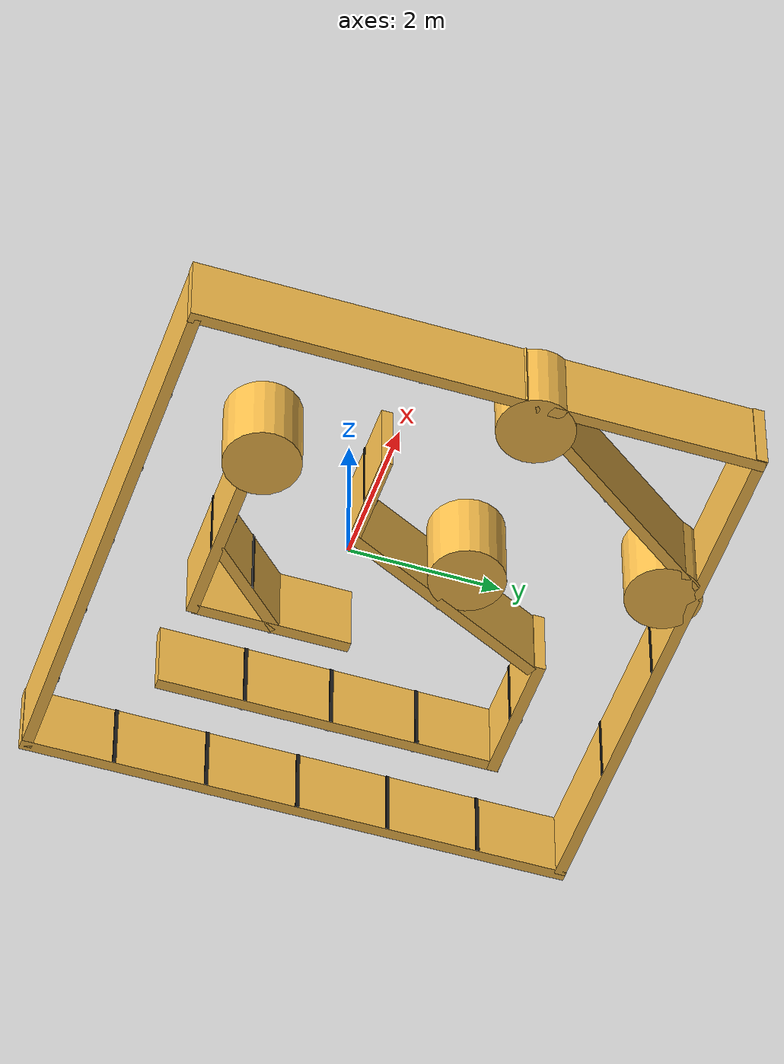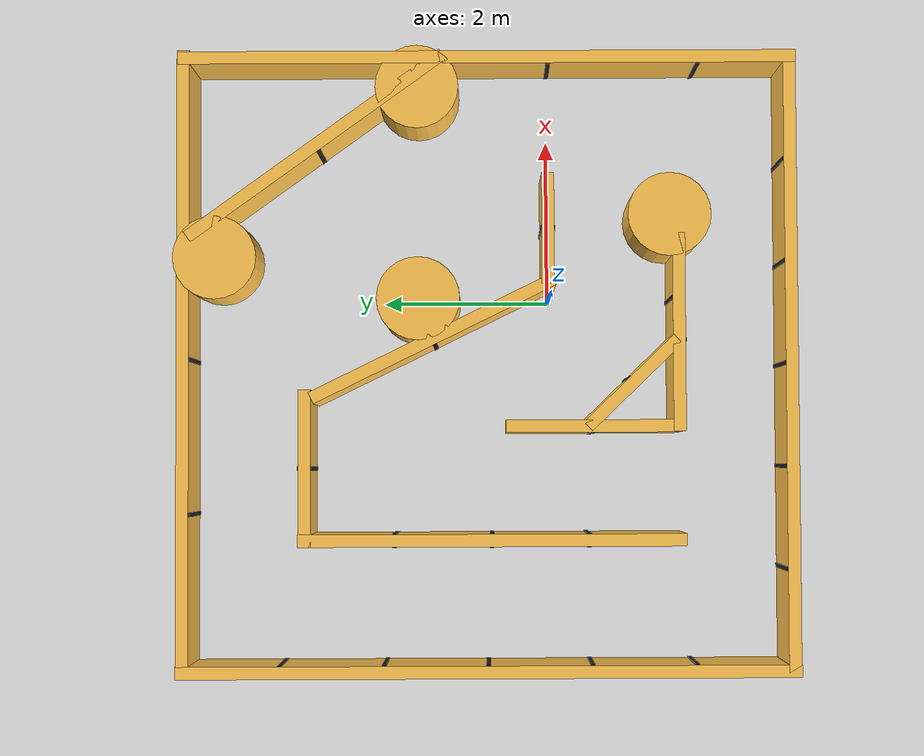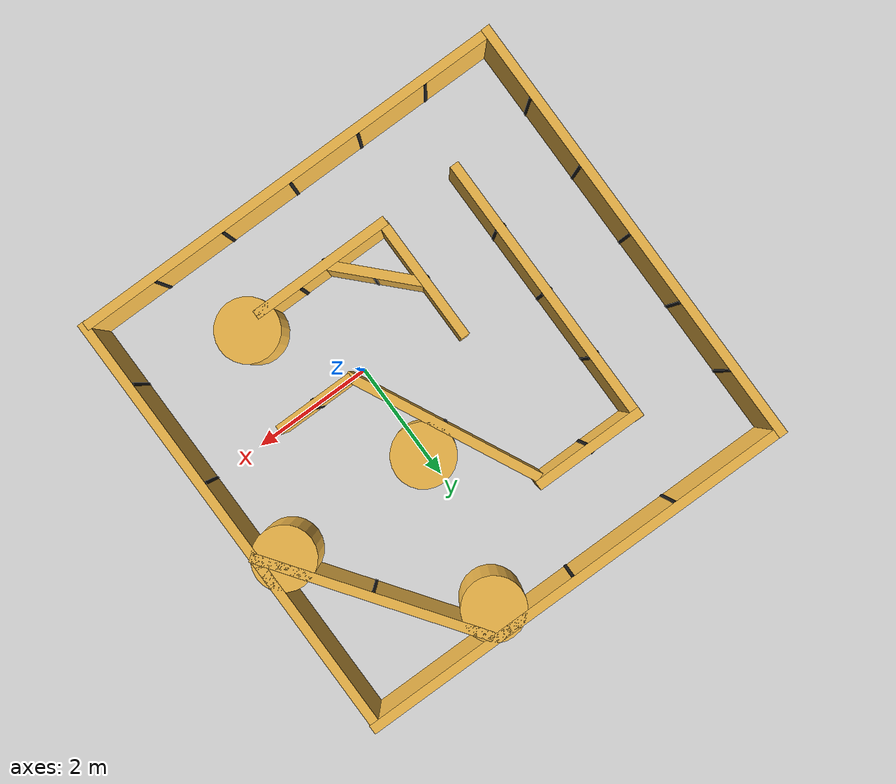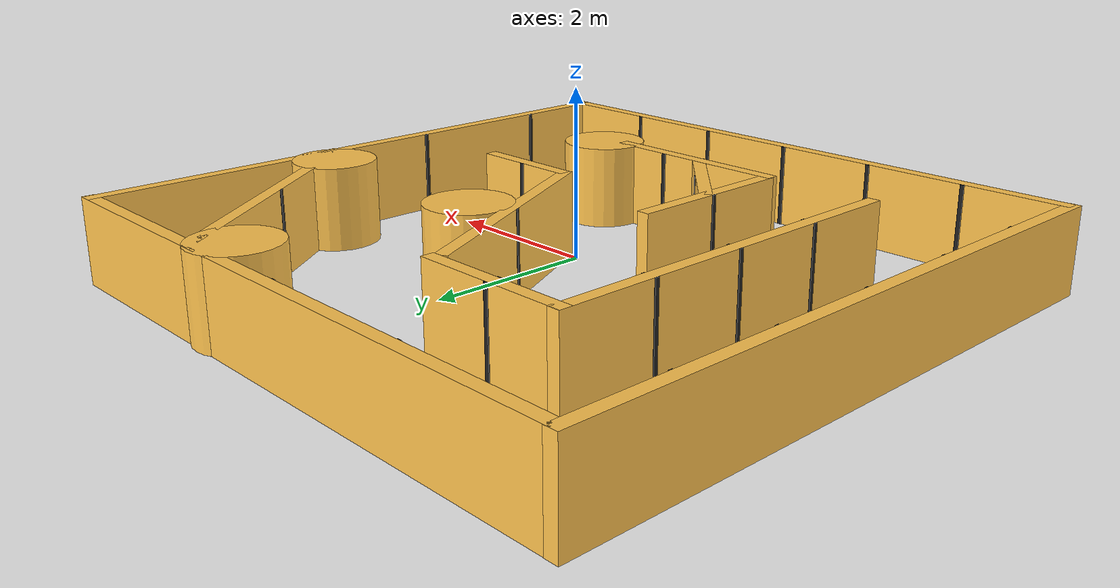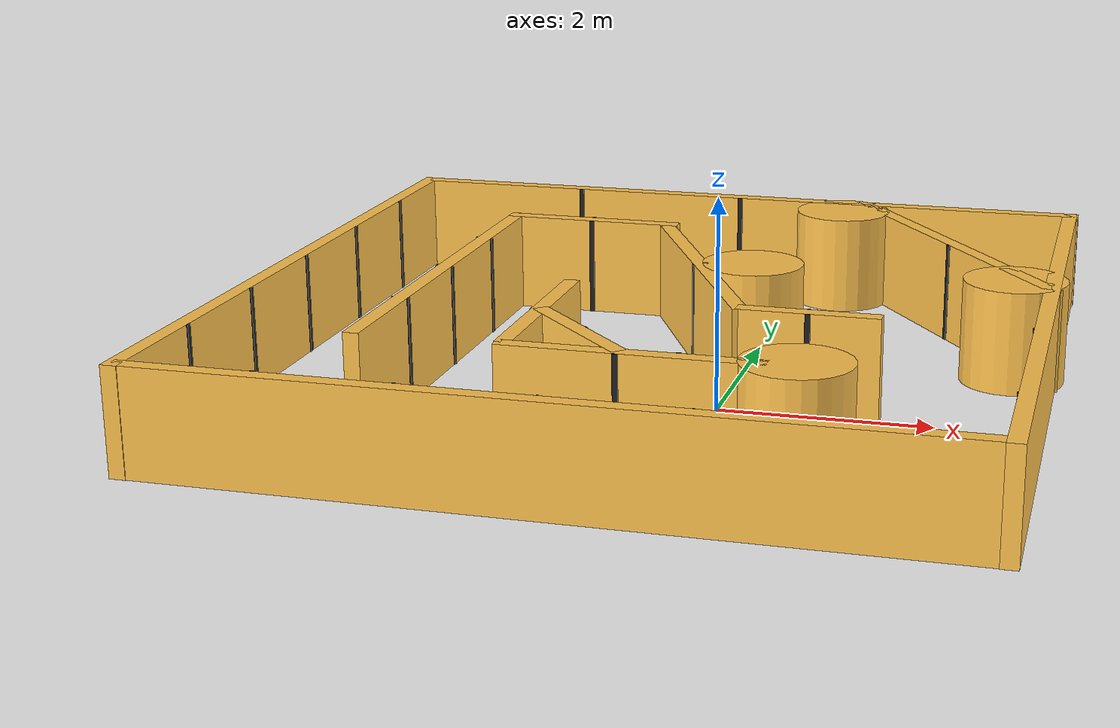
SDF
<?xml version='1.0'?>
<sdf version='1.5'>
  <model name='Maze_ql_1'>
    <link name='Wall_10'>
      <pose frame=''>-2.02568 2.92333 0 0 -0 3.14159</pose>
      <self_collide>0</self_collide>
      <kinematic>0</kinematic>
      <visual name='Wall_10_Visual'>
        <pose frame=''>0 0 0.5 0 -0 0</pose>
        <geometry>
          <box>
            <size>1.8711 0.15 1</size>
          </box>
        </geometry>
        <material>
          <script>
            <uri>file://media/materials/scripts/gazebo.material</uri>
            <name>Gazebo/Grey</name>
          </script>
          <ambient>1 0.764706 0.305882 1</ambient>
          <diffuse>0.7 0.7 0.7 1</diffuse>
          <specular>0.01 0.01 0.01 1</specular>
          <emissive>0 0 0 1</emissive>
          <shader type='pixel'/>
        </material>
        <cast_shadows>1</cast_shadows>
        <transparency>0</transparency>
      </visual>
      <collision name='Wall_10_Collision'>
        <laser_retro>0</laser_retro>
        <max_contacts>10</max_contacts>
        <pose frame=''>0 0 0.5 0 -0 0</pose>
        <geometry>
          <box>
            <size>1.8711 0.15 1</size>
          </box>
        </geometry>
        <surface>
          <friction>
            <ode>
              <mu>1</mu>
              <mu2>1</mu2>
              <fdir1>0 0 0</fdir1>
              <slip1>0</slip1>
              <slip2>0</slip2>
            </ode>
          </friction>
          <bounce>
            <restitution_coefficient>0</restitution_coefficient>
            <threshold>1e+06</threshold>
          </bounce>
          <contact>
            <collide_without_contact>0</collide_without_contact>
            <collide_without_contact_bitmask>1</collide_without_contact_bitmask>
            <collide_bitmask>1</collide_bitmask>
            <ode>
              <soft_cfm>0</soft_cfm>
              <soft_erp>0.2</soft_erp>
              <kp>1e+13</kp>
              <kd>1</kd>
              <max_vel>0.01</max_vel>
              <min_depth>0</min_depth>
            </ode>
            <bullet>
              <split_impulse>1</split_impulse>
              <split_impulse_penetration_threshold>-0.01</split_impulse_penetration_threshold>
              <soft_cfm>0</soft_cfm>
              <soft_erp>0.2</soft_erp>
              <kp>1e+13</kp>
              <kd>1</kd>
            </bullet>
          </contact>
        </surface>
      </collision>
    </link>
    <link name='Wall_11'>
      <pose frame=''>-2.887 0.69235 0 0 0 -1.5708</pose>
      <self_collide>0</self_collide>
      <kinematic>0</kinematic>
      <visual name='Wall_11_Visual'>
        <pose frame=''>0 0 0.5 0 -0 0</pose>
        <geometry>
          <box>
            <size>4.62378 0.15 1</size>
          </box>
        </geometry>
        <material>
          <script>
            <uri>file://media/materials/scripts/gazebo.material</uri>
            <name>Gazebo/Grey</name>
          </script>
          <ambient>1 0.764706 0.305882 1</ambient>
          <diffuse>0.7 0.7 0.7 1</diffuse>
          <specular>0.01 0.01 0.01 1</specular>
          <emissive>0 0 0 1</emissive>
          <shader type='pixel'/>
        </material>
        <cast_shadows>1</cast_shadows>
        <transparency>0</transparency>
      </visual>
      <collision name='Wall_11_Collision'>
        <laser_retro>0</laser_retro>
        <max_contacts>10</max_contacts>
        <pose frame=''>0 0 0.5 0 -0 0</pose>
        <geometry>
          <box>
            <size>4.62378 0.15 1</size>
          </box>
        </geometry>
        <surface>
          <friction>
            <ode>
              <mu>1</mu>
              <mu2>1</mu2>
              <fdir1>0 0 0</fdir1>
              <slip1>0</slip1>
              <slip2>0</slip2>
            </ode>
          </friction>
          <bounce>
            <restitution_coefficient>0</restitution_coefficient>
            <threshold>1e+06</threshold>
          </bounce>
          <contact>
            <collide_without_contact>0</collide_without_contact>
            <collide_without_contact_bitmask>1</collide_without_contact_bitmask>
            <collide_bitmask>1</collide_bitmask>
            <ode>
              <soft_cfm>0</soft_cfm>
              <soft_erp>0.2</soft_erp>
              <kp>1e+13</kp>
              <kd>1</kd>
              <max_vel>0.01</max_vel>
              <min_depth>0</min_depth>
            </ode>
            <bullet>
              <split_impulse>1</split_impulse>
              <split_impulse_penetration_threshold>-0.01</split_impulse_penetration_threshold>
              <soft_cfm>0</soft_cfm>
              <soft_erp>0.2</soft_erp>
              <kp>1e+13</kp>
              <kd>1</kd>
            </bullet>
          </contact>
        </surface>
      </collision>
    </link>
    <link name='Wall_11_clone'>
      <pose frame=''>-4.44208 0.738947 0 0 0 -1.5708</pose>
      <self_collide>0</self_collide>
      <kinematic>0</kinematic>
      <visual name='ModelPreview_2::Wall_11_clone::Wall_11_Visual'>
        <pose frame=''>0 0 0.5 0 -0 0</pose>
        <geometry>
          <box>
            <size>7.42809 0.15 1</size>
          </box>
        </geometry>
        <material>
          <script>
            <uri>file://media/materials/scripts/gazebo.material</uri>
            <name>Gazebo/Grey</name>
          </script>
          <ambient>1 0.764706 0.305882 1</ambient>
          <diffuse>0.7 0.7 0.7 1</diffuse>
          <specular>0.01 0.01 0.01 1</specular>
          <emissive>0 0 0 1</emissive>
          <shader type='pixel'/>
        </material>
        <cast_shadows>1</cast_shadows>
        <transparency>0</transparency>
      </visual>
      <collision name='Wall_11_Collision'>
        <laser_retro>0</laser_retro>
        <max_contacts>10</max_contacts>
        <pose frame=''>0 0 0.5 0 -0 0</pose>
        <geometry>
          <box>
            <size>7.42809 0.15 1</size>
          </box>
        </geometry>
        <surface>
          <friction>
            <ode>
              <mu>1</mu>
              <mu2>1</mu2>
              <fdir1>0 0 0</fdir1>
              <slip1>0</slip1>
              <slip2>0</slip2>
            </ode>
          </friction>
          <bounce>
            <restitution_coefficient>0</restitution_coefficient>
            <threshold>1e+06</threshold>
          </bounce>
          <contact>
            <collide_without_contact>0</collide_without_contact>
            <collide_without_contact_bitmask>1</collide_without_contact_bitmask>
            <collide_bitmask>1</collide_bitmask>
            <ode>
              <soft_cfm>0</soft_cfm>
              <soft_erp>0.2</soft_erp>
              <kp>1e+13</kp>
              <kd>1</kd>
              <max_vel>0.01</max_vel>
              <min_depth>0</min_depth>
            </ode>
            <bullet>
              <split_impulse>1</split_impulse>
              <split_impulse_penetration_threshold>-0.01</split_impulse_penetration_threshold>
              <soft_cfm>0</soft_cfm>
              <soft_erp>0.2</soft_erp>
              <kp>1e+13</kp>
              <kd>1</kd>
            </bullet>
          </contact>
        </surface>
      </collision>
    </link>
    <link name='Wall_14'>
      <pose frame=''>-0.409926 -1.55115 0 0 -0 3.14159</pose>
      <self_collide>0</self_collide>
      <kinematic>0</kinematic>
      <visual name='Wall_14_Visual'>
        <pose frame=''>0 0 0.5 0 -0 0</pose>
        <geometry>
          <box>
            <size>2.36648 0.15 1</size>
          </box>
        </geometry>
        <material>
          <script>
            <uri>file://media/materials/scripts/gazebo.material</uri>
            <name>Gazebo/Grey</name>
          </script>
          <ambient>1 0.764706 0.305882 1</ambient>
          <diffuse>0.7 0.7 0.7 1</diffuse>
          <specular>0.01 0.01 0.01 1</specular>
          <emissive>0 0 0 1</emissive>
          <shader type='pixel'/>
        </material>
        <cast_shadows>1</cast_shadows>
        <transparency>0</transparency>
      </visual>
      <collision name='Wall_14_Collision'>
        <laser_retro>0</laser_retro>
        <max_contacts>10</max_contacts>
        <pose frame=''>0 0 0.5 0 -0 0</pose>
        <geometry>
          <box>
            <size>2.36648 0.15 1</size>
          </box>
        </geometry>
        <surface>
          <friction>
            <ode>
              <mu>1</mu>
              <mu2>1</mu2>
              <fdir1>0 0 0</fdir1>
              <slip1>0</slip1>
              <slip2>0</slip2>
            </ode>
          </friction>
          <bounce>
            <restitution_coefficient>0</restitution_coefficient>
            <threshold>1e+06</threshold>
          </bounce>
          <contact>
            <collide_without_contact>0</collide_without_contact>
            <collide_without_contact_bitmask>1</collide_without_contact_bitmask>
            <collide_bitmask>1</collide_bitmask>
            <ode>
              <soft_cfm>0</soft_cfm>
              <soft_erp>0.2</soft_erp>
              <kp>1e+13</kp>
              <kd>1</kd>
              <max_vel>0.01</max_vel>
              <min_depth>0</min_depth>
            </ode>
            <bullet>
              <split_impulse>1</split_impulse>
              <split_impulse_penetration_threshold>-0.01</split_impulse_penetration_threshold>
              <soft_cfm>0</soft_cfm>
              <soft_erp>0.2</soft_erp>
              <kp>1e+13</kp>
              <kd>1</kd>
            </bullet>
          </contact>
        </surface>
      </collision>
    </link>
    <link name='Wall_15'>
      <pose frame=''>-1.53187 -0.513425 0 0 -0 1.5708</pose>
      <self_collide>0</self_collide>
      <kinematic>0</kinematic>
      <visual name='Wall_15_Visual'>
        <pose frame=''>0 0 0.5 0 -0 0</pose>
        <geometry>
          <box>
            <size>2.06622 0.15 1</size>
          </box>
        </geometry>
        <material>
          <script>
            <uri>file://media/materials/scripts/gazebo.material</uri>
            <name>Gazebo/Grey</name>
          </script>
          <ambient>1 0.764706 0.305882 1</ambient>
          <diffuse>0.7 0.7 0.7 1</diffuse>
          <specular>0.01 0.01 0.01 1</specular>
          <emissive>0 0 0 1</emissive>
          <shader type='pixel'/>
        </material>
        <cast_shadows>1</cast_shadows>
        <transparency>0</transparency>
      </visual>
      <collision name='Wall_15_Collision'>
        <laser_retro>0</laser_retro>
        <max_contacts>10</max_contacts>
        <pose frame=''>0 0 0.5 0 -0 0</pose>
        <geometry>
          <box>
            <size>2.06622 0.15 1</size>
          </box>
        </geometry>
        <surface>
          <friction>
            <ode>
              <mu>1</mu>
              <mu2>1</mu2>
              <fdir1>0 0 0</fdir1>
              <slip1>0</slip1>
              <slip2>0</slip2>
            </ode>
          </friction>
          <bounce>
            <restitution_coefficient>0</restitution_coefficient>
            <threshold>1e+06</threshold>
          </bounce>
          <contact>
            <collide_without_contact>0</collide_without_contact>
            <collide_without_contact_bitmask>1</collide_without_contact_bitmask>
            <collide_bitmask>1</collide_bitmask>
            <ode>
              <soft_cfm>0</soft_cfm>
              <soft_erp>0.2</soft_erp>
              <kp>1e+13</kp>
              <kd>1</kd>
              <max_vel>0.01</max_vel>
              <min_depth>0</min_depth>
            </ode>
            <bullet>
              <split_impulse>1</split_impulse>
              <split_impulse_penetration_threshold>-0.01</split_impulse_penetration_threshold>
              <soft_cfm>0</soft_cfm>
              <soft_erp>0.2</soft_erp>
              <kp>1e+13</kp>
              <kd>1</kd>
            </bullet>
          </contact>
        </surface>
      </collision>
    </link>
    <link name='Wall_19'>
      <pose frame=''>0.837565 0.010614 0 0 -0 3.14159</pose>
      <self_collide>0</self_collide>
      <kinematic>0</kinematic>
      <visual name='Wall_19_Visual'>
        <pose frame=''>0 0 0.5 0 -0 0</pose>
        <geometry>
          <box>
            <size>1.32777 0.15 1</size>
          </box>
        </geometry>
        <material>
          <script>
            <uri>file://media/materials/scripts/gazebo.material</uri>
            <name>Gazebo/Grey</name>
          </script>
          <ambient>1 0.764706 0.305882 1</ambient>
          <diffuse>0.7 0.7 0.7 1</diffuse>
          <specular>0.01 0.01 0.01 1</specular>
          <emissive>0 0 0 1</emissive>
          <shader type='pixel'/>
        </material>
        <cast_shadows>1</cast_shadows>
        <transparency>0</transparency>
      </visual>
      <collision name='Wall_19_Collision'>
        <laser_retro>0</laser_retro>
        <max_contacts>10</max_contacts>
        <pose frame=''>0 0 0.5 0 -0 0</pose>
        <geometry>
          <box>
            <size>1.32777 0.15 1</size>
          </box>
        </geometry>
        <surface>
          <friction>
            <ode>
              <mu>1</mu>
              <mu2>1</mu2>
              <fdir1>0 0 0</fdir1>
              <slip1>0</slip1>
              <slip2>0</slip2>
            </ode>
          </friction>
          <bounce>
            <restitution_coefficient>0</restitution_coefficient>
            <threshold>1e+06</threshold>
          </bounce>
          <contact>
            <collide_without_contact>0</collide_without_contact>
            <collide_without_contact_bitmask>1</collide_without_contact_bitmask>
            <collide_bitmask>1</collide_bitmask>
            <ode>
              <soft_cfm>0</soft_cfm>
              <soft_erp>0.2</soft_erp>
              <kp>1e+13</kp>
              <kd>1</kd>
              <max_vel>0.01</max_vel>
              <min_depth>0</min_depth>
            </ode>
            <bullet>
              <split_impulse>1</split_impulse>
              <split_impulse_penetration_threshold>-0.01</split_impulse_penetration_threshold>
              <soft_cfm>0</soft_cfm>
              <soft_erp>0.2</soft_erp>
              <kp>1e+13</kp>
              <kd>1</kd>
            </bullet>
          </contact>
        </surface>
      </collision>
    </link>
    <link name='Wall_20'>
      <pose frame=''>-0.484506 1.39698 0 0 -0 2.02352</pose>
      <self_collide>0</self_collide>
      <kinematic>0</kinematic>
      <visual name='Wall_20_Visual'>
        <pose frame=''>0 0 0.5 0 -0 0</pose>
        <geometry>
          <box>
            <size>3.22686 0.15 1</size>
          </box>
        </geometry>
        <material>
          <script>
            <uri>file://media/materials/scripts/gazebo.material</uri>
            <name>Gazebo/Grey</name>
          </script>
          <ambient>1 0.764706 0.305882 1</ambient>
          <diffuse>0.7 0.7 0.7 1</diffuse>
          <specular>0.01 0.01 0.01 1</specular>
          <emissive>0 0 0 1</emissive>
          <shader type='pixel'/>
        </material>
        <cast_shadows>1</cast_shadows>
        <transparency>0</transparency>
      </visual>
      <collision name='Wall_20_Collision'>
        <laser_retro>0</laser_retro>
        <max_contacts>10</max_contacts>
        <pose frame=''>0 0 0.5 0 -0 0</pose>
        <geometry>
          <box>
            <size>3.22686 0.15 1</size>
          </box>
        </geometry>
        <surface>
          <friction>
            <ode>
              <mu>1</mu>
              <mu2>1</mu2>
              <fdir1>0 0 0</fdir1>
              <slip1>0</slip1>
              <slip2>0</slip2>
            </ode>
          </friction>
          <bounce>
            <restitution_coefficient>0</restitution_coefficient>
            <threshold>1e+06</threshold>
          </bounce>
          <contact>
            <collide_without_contact>0</collide_without_contact>
            <collide_without_contact_bitmask>1</collide_without_contact_bitmask>
            <collide_bitmask>1</collide_bitmask>
            <ode>
              <soft_cfm>0</soft_cfm>
              <soft_erp>0.2</soft_erp>
              <kp>1e+13</kp>
              <kd>1</kd>
              <max_vel>0.01</max_vel>
              <min_depth>0</min_depth>
            </ode>
            <bullet>
              <split_impulse>1</split_impulse>
              <split_impulse_penetration_threshold>-0.01</split_impulse_penetration_threshold>
              <soft_cfm>0</soft_cfm>
              <soft_erp>0.2</soft_erp>
              <kp>1e+13</kp>
              <kd>1</kd>
            </bullet>
          </contact>
        </surface>
      </collision>
    </link>
    <link name='Wall_24'>
      <pose frame=''>1.8412 2.79579 0 0 0 -0.948986</pose>
      <self_collide>0</self_collide>
      <kinematic>0</kinematic>
      <visual name='Wall_24_Visual'>
        <pose frame=''>0 0 0.5 0 -0 0</pose>
        <geometry>
          <box>
            <size>3.76645 0.15 1</size>
          </box>
        </geometry>
        <material>
          <script>
            <uri>file://media/materials/scripts/gazebo.material</uri>
            <name>Gazebo/Grey</name>
          </script>
          <ambient>1 0.764706 0.305882 1</ambient>
          <diffuse>0.7 0.7 0.7 1</diffuse>
          <specular>0.01 0.01 0.01 1</specular>
          <emissive>0 0 0 1</emissive>
          <shader type='pixel'/>
        </material>
        <cast_shadows>1</cast_shadows>
        <transparency>0</transparency>
      </visual>
      <collision name='Wall_24_Collision'>
        <laser_retro>0</laser_retro>
        <max_contacts>10</max_contacts>
        <pose frame=''>0 0 0.5 0 -0 0</pose>
        <geometry>
          <box>
            <size>3.76645 0.15 1</size>
          </box>
        </geometry>
        <surface>
          <friction>
            <ode>
              <mu>1</mu>
              <mu2>1</mu2>
              <fdir1>0 0 0</fdir1>
              <slip1>0</slip1>
              <slip2>0</slip2>
            </ode>
          </friction>
          <bounce>
            <restitution_coefficient>0</restitution_coefficient>
            <threshold>1e+06</threshold>
          </bounce>
          <contact>
            <collide_without_contact>0</collide_without_contact>
            <collide_without_contact_bitmask>1</collide_without_contact_bitmask>
            <collide_bitmask>1</collide_bitmask>
            <ode>
              <soft_cfm>0</soft_cfm>
              <soft_erp>0.2</soft_erp>
              <kp>1e+13</kp>
              <kd>1</kd>
              <max_vel>0.01</max_vel>
              <min_depth>0</min_depth>
            </ode>
            <bullet>
              <split_impulse>1</split_impulse>
              <split_impulse_penetration_threshold>-0.01</split_impulse_penetration_threshold>
              <soft_cfm>0</soft_cfm>
              <soft_erp>0.2</soft_erp>
              <kp>1e+13</kp>
              <kd>1</kd>
            </bullet>
          </contact>
        </surface>
      </collision>
    </link>
    <link name='Wall_24_clone'>
      <pose frame=''>-1.0172 -1.00075 0 0 0 -0.803995</pose>
      <self_collide>0</self_collide>
      <kinematic>0</kinematic>
      <visual name='ModelPreview_2::Wall_24_clone::Wall_24_Visual'>
        <pose frame=''>0 0 0.5 0 -0 0</pose>
        <geometry>
          <box>
            <size>1.5 0.15 1</size>
          </box>
        </geometry>
        <material>
          <script>
            <uri>file://media/materials/scripts/gazebo.material</uri>
            <name>Gazebo/Grey</name>
          </script>
          <ambient>1 0.764706 0.305882 1</ambient>
          <diffuse>0.7 0.7 0.7 1</diffuse>
          <specular>0.01 0.01 0.01 1</specular>
          <emissive>0 0 0 1</emissive>
          <shader type='pixel'/>
        </material>
        <cast_shadows>1</cast_shadows>
        <transparency>0</transparency>
      </visual>
      <collision name='Wall_24_Collision'>
        <laser_retro>0</laser_retro>
        <max_contacts>10</max_contacts>
        <pose frame=''>0 0 0.5 0 -0 0</pose>
        <geometry>
          <box>
            <size>1.5 0.15 1</size>
          </box>
        </geometry>
        <surface>
          <friction>
            <ode>
              <mu>1</mu>
              <mu2>1</mu2>
              <fdir1>0 0 0</fdir1>
              <slip1>0</slip1>
              <slip2>0</slip2>
            </ode>
          </friction>
          <bounce>
            <restitution_coefficient>0</restitution_coefficient>
            <threshold>1e+06</threshold>
          </bounce>
          <contact>
            <collide_without_contact>0</collide_without_contact>
            <collide_without_contact_bitmask>1</collide_without_contact_bitmask>
            <collide_bitmask>1</collide_bitmask>
            <ode>
              <soft_cfm>0</soft_cfm>
              <soft_erp>0.2</soft_erp>
              <kp>1e+13</kp>
              <kd>1</kd>
              <max_vel>0.01</max_vel>
              <min_depth>0</min_depth>
            </ode>
            <bullet>
              <split_impulse>1</split_impulse>
              <split_impulse_penetration_threshold>-0.01</split_impulse_penetration_threshold>
              <soft_cfm>0</soft_cfm>
              <soft_erp>0.2</soft_erp>
              <kp>1e+13</kp>
              <kd>1</kd>
            </bullet>
          </contact>
        </surface>
      </collision>
    </link>
    <link name='Wall_6'>
      <pose frame=''>-0.787021 -2.89307 0 0 -0 0</pose>
      <self_collide>0</self_collide>
      <kinematic>0</kinematic>
      <visual name='Wall_6_Visual'>
        <pose frame=''>0 0 0.5 0 -0 0</pose>
        <geometry>
          <box>
            <size>7.34986 0.15 1</size>
          </box>
        </geometry>
        <material>
          <script>
            <uri>file://media/materials/scripts/gazebo.material</uri>
            <name>Gazebo/Grey</name>
          </script>
          <ambient>1 0.764706 0.305882 1</ambient>
          <diffuse>0.7 0.7 0.7 1</diffuse>
          <specular>0.01 0.01 0.01 1</specular>
          <emissive>0 0 0 1</emissive>
          <shader type='pixel'/>
        </material>
        <cast_shadows>1</cast_shadows>
        <transparency>0</transparency>
      </visual>
      <collision name='Wall_6_Collision'>
        <laser_retro>0</laser_retro>
        <max_contacts>10</max_contacts>
        <pose frame=''>0 0 0.5 0 -0 0</pose>
        <geometry>
          <box>
            <size>7.34986 0.15 1</size>
          </box>
        </geometry>
        <surface>
          <friction>
            <ode>
              <mu>1</mu>
              <mu2>1</mu2>
              <fdir1>0 0 0</fdir1>
              <slip1>0</slip1>
              <slip2>0</slip2>
            </ode>
          </friction>
          <bounce>
            <restitution_coefficient>0</restitution_coefficient>
            <threshold>1e+06</threshold>
          </bounce>
          <contact>
            <collide_without_contact>0</collide_without_contact>
            <collide_without_contact_bitmask>1</collide_without_contact_bitmask>
            <collide_bitmask>1</collide_bitmask>
            <ode>
              <soft_cfm>0</soft_cfm>
              <soft_erp>0.2</soft_erp>
              <kp>1e+13</kp>
              <kd>1</kd>
              <max_vel>0.01</max_vel>
              <min_depth>0</min_depth>
            </ode>
            <bullet>
              <split_impulse>1</split_impulse>
              <split_impulse_penetration_threshold>-0.01</split_impulse_penetration_threshold>
              <soft_cfm>0</soft_cfm>
              <soft_erp>0.2</soft_erp>
              <kp>1e+13</kp>
              <kd>1</kd>
            </bullet>
          </contact>
        </surface>
      </collision>
    </link>
    <link name='Wall_6_clone'>
      <pose frame=''>-0.718431 4.37517 0 0 -0 0</pose>
      <self_collide>0</self_collide>
      <kinematic>0</kinematic>
      <visual name='ModelPreview_2::Wall_6_clone::Wall_6_Visual'>
        <pose frame=''>0 0 0.5 0 -0 0</pose>
        <geometry>
          <box>
            <size>7.41907 0.15 1</size>
          </box>
        </geometry>
        <material>
          <script>
            <uri>file://media/materials/scripts/gazebo.material</uri>
            <name>Gazebo/Grey</name>
          </script>
          <ambient>1 0.764706 0.305882 1</ambient>
          <diffuse>0.7 0.7 0.7 1</diffuse>
          <specular>0.01 0.01 0.01 1</specular>
          <emissive>0 0 0 1</emissive>
          <shader type='pixel'/>
        </material>
        <cast_shadows>1</cast_shadows>
        <transparency>0</transparency>
      </visual>
      <collision name='Wall_6_Collision'>
        <laser_retro>0</laser_retro>
        <max_contacts>10</max_contacts>
        <pose frame=''>0 0 0.5 0 -0 0</pose>
        <geometry>
          <box>
            <size>7.41907 0.15 1</size>
          </box>
        </geometry>
        <surface>
          <friction>
            <ode>
              <mu>1</mu>
              <mu2>1</mu2>
              <fdir1>0 0 0</fdir1>
              <slip1>0</slip1>
              <slip2>0</slip2>
            </ode>
          </friction>
          <bounce>
            <restitution_coefficient>0</restitution_coefficient>
            <threshold>1e+06</threshold>
          </bounce>
          <contact>
            <collide_without_contact>0</collide_without_contact>
            <collide_without_contact_bitmask>1</collide_without_contact_bitmask>
            <collide_bitmask>1</collide_bitmask>
            <ode>
              <soft_cfm>0</soft_cfm>
              <soft_erp>0.2</soft_erp>
              <kp>1e+13</kp>
              <kd>1</kd>
              <max_vel>0.01</max_vel>
              <min_depth>0</min_depth>
            </ode>
            <bullet>
              <split_impulse>1</split_impulse>
              <split_impulse_penetration_threshold>-0.01</split_impulse_penetration_threshold>
              <soft_cfm>0</soft_cfm>
              <soft_erp>0.2</soft_erp>
              <kp>1e+13</kp>
              <kd>1</kd>
            </bullet>
          </contact>
        </surface>
      </collision>
    </link>
    <link name='Wall_7'>
      <pose frame=''>2.90228 0.736783 0 0 -0 1.5708</pose>
      <self_collide>0</self_collide>
      <kinematic>0</kinematic>
      <visual name='Wall_7_Visual'>
        <pose frame=''>0 0 0.5 0 -0 0</pose>
        <geometry>
          <box>
            <size>7.42238 0.15 1</size>
          </box>
        </geometry>
        <material>
          <script>
            <uri>file://media/materials/scripts/gazebo.material</uri>
            <name>Gazebo/Grey</name>
          </script>
          <ambient>1 0.764706 0.305882 1</ambient>
          <diffuse>0.7 0.7 0.7 1</diffuse>
          <specular>0.01 0.01 0.01 1</specular>
          <emissive>0 0 0 1</emissive>
          <shader type='pixel'/>
        </material>
        <cast_shadows>1</cast_shadows>
        <transparency>0</transparency>
      </visual>
      <collision name='Wall_7_Collision'>
        <laser_retro>0</laser_retro>
        <max_contacts>10</max_contacts>
        <pose frame=''>0 0 0.5 0 -0 0</pose>
        <geometry>
          <box>
            <size>7.42238 0.15 1</size>
          </box>
        </geometry>
        <surface>
          <friction>
            <ode>
              <mu>1</mu>
              <mu2>1</mu2>
              <fdir1>0 0 0</fdir1>
              <slip1>0</slip1>
              <slip2>0</slip2>
            </ode>
          </friction>
          <bounce>
            <restitution_coefficient>0</restitution_coefficient>
            <threshold>1e+06</threshold>
          </bounce>
          <contact>
            <collide_without_contact>0</collide_without_contact>
            <collide_without_contact_bitmask>1</collide_without_contact_bitmask>
            <collide_bitmask>1</collide_bitmask>
            <ode>
              <soft_cfm>0</soft_cfm>
              <soft_erp>0.2</soft_erp>
              <kp>1e+13</kp>
              <kd>1</kd>
              <max_vel>0.01</max_vel>
              <min_depth>0</min_depth>
            </ode>
            <bullet>
              <split_impulse>1</split_impulse>
              <split_impulse_penetration_threshold>-0.01</split_impulse_penetration_threshold>
              <soft_cfm>0</soft_cfm>
              <soft_erp>0.2</soft_erp>
              <kp>1e+13</kp>
              <kd>1</kd>
            </bullet>
          </contact>
        </surface>
      </collision>
    </link>
    <link name='link_1'>
      <pose frame=''>1 -1.44562 0.5 0 -0 0</pose>
      <visual name='visual'>
        <pose frame=''>0 0 0 0 -0 0</pose>
        <geometry>
          <cylinder>
            <radius>0.5</radius>
            <length>1</length>
          </cylinder>
        </geometry>
        <material>
          <script>
            <uri>file://media/materials/scripts/gazebo.material</uri>
            <name>Gazebo/Grey</name>
          </script>
          <ambient>1 0.764706 0.305882 1</ambient>
          <diffuse>0.7 0.7 0.7 1</diffuse>
          <specular>0.01 0.01 0.01 1</specular>
          <emissive>0 0 0 1</emissive>
          <shader type='pixel'/>
        </material>
        <cast_shadows>1</cast_shadows>
        <transparency>0</transparency>
      </visual>
      <collision name='collision'>
        <laser_retro>0</laser_retro>
        <max_contacts>10</max_contacts>
        <pose frame=''>0 0 0 0 -0 0</pose>
        <geometry>
          <cylinder>
            <radius>0.5</radius>
            <length>1</length>
          </cylinder>
        </geometry>
        <surface>
          <friction>
            <ode>
              <mu>1</mu>
              <mu2>1</mu2>
              <fdir1>0 0 0</fdir1>
              <slip1>0</slip1>
              <slip2>0</slip2>
            </ode>
          </friction>
          <bounce>
            <restitution_coefficient>0</restitution_coefficient>
            <threshold>1e+06</threshold>
          </bounce>
          <contact>
            <collide_without_contact>0</collide_without_contact>
            <collide_without_contact_bitmask>1</collide_without_contact_bitmask>
            <collide_bitmask>1</collide_bitmask>
            <ode>
              <soft_cfm>0</soft_cfm>
              <soft_erp>0.2</soft_erp>
              <kp>1e+13</kp>
              <kd>1</kd>
              <max_vel>0.01</max_vel>
              <min_depth>0</min_depth>
            </ode>
            <bullet>
              <split_impulse>1</split_impulse>
              <split_impulse_penetration_threshold>-0.01</split_impulse_penetration_threshold>
              <soft_cfm>0</soft_cfm>
              <soft_erp>0.2</soft_erp>
              <kp>1e+13</kp>
              <kd>1</kd>
            </bullet>
          </contact>
        </surface>
      </collision>
    </link>
    <link name='link_2'>
      <pose frame=''>0.498835 4 0.5 0 -0 0</pose>
      <visual name='visual'>
        <pose frame=''>0 0 0 0 -0 0</pose>
        <geometry>
          <cylinder>
            <radius>0.5</radius>
            <length>1</length>
          </cylinder>
        </geometry>
        <material>
          <script>
            <uri>file://media/materials/scripts/gazebo.material</uri>
            <name>Gazebo/Grey</name>
          </script>
          <ambient>1 0.764706 0.305882 1</ambient>
          <diffuse>0.7 0.7 0.7 1</diffuse>
          <specular>0.01 0.01 0.01 1</specular>
          <emissive>0 0 0 1</emissive>
          <shader type='pixel'/>
        </material>
        <cast_shadows>1</cast_shadows>
        <transparency>0</transparency>
        <cast_shadows>1</cast_shadows>
        <transparency>0</transparency>
      </visual>
      <collision name='collision'>
        <laser_retro>0</laser_retro>
        <max_contacts>10</max_contacts>
        <pose frame=''>0 0 0 0 -0 0</pose>
        <geometry>
          <cylinder>
            <radius>0.5</radius>
            <length>1</length>
          </cylinder>
        </geometry>
        <surface>
          <friction>
            <ode>
              <mu>1</mu>
              <mu2>1</mu2>
              <fdir1>0 0 0</fdir1>
              <slip1>0</slip1>
              <slip2>0</slip2>
            </ode>
          </friction>
          <bounce>
            <restitution_coefficient>0</restitution_coefficient>
            <threshold>1e+06</threshold>
          </bounce>
          <contact>
            <collide_without_contact>0</collide_without_contact>
            <collide_without_contact_bitmask>1</collide_without_contact_bitmask>
            <collide_bitmask>1</collide_bitmask>
            <ode>
              <soft_cfm>0</soft_cfm>
              <soft_erp>0.2</soft_erp>
              <kp>1e+13</kp>
              <kd>1</kd>
              <max_vel>0.01</max_vel>
              <min_depth>0</min_depth>
            </ode>
            <bullet>
              <split_impulse>1</split_impulse>
              <split_impulse_penetration_threshold>-0.01</split_impulse_penetration_threshold>
              <soft_cfm>0</soft_cfm>
              <soft_erp>0.2</soft_erp>
              <kp>1e+13</kp>
              <kd>1</kd>
            </bullet>
          </contact>
        </surface>
      </collision>
    </link>
    <link name='link_3'>
      <pose frame=''>0 1.56543 0.5 0 -0 0</pose>
      <visual name='visual'>
        <pose frame=''>0 0 0 0 -0 0</pose>
        <geometry>
          <cylinder>
            <radius>0.5</radius>
            <length>1</length>
          </cylinder>
        </geometry>
        <material>
          <script>
            <uri>file://media/materials/scripts/gazebo.material</uri>
            <name>Gazebo/Grey</name>
          </script>
          <ambient>1 0.764706 0.305882 1</ambient>
          <diffuse>0.7 0.7 0.7 1</diffuse>
          <specular>0.01 0.01 0.01 1</specular>
          <emissive>0 0 0 1</emissive>
          <shader type='pixel'/>
        </material>
        <cast_shadows>1</cast_shadows>
        <transparency>0</transparency>
        <cast_shadows>1</cast_shadows>
        <transparency>0</transparency>
      </visual>
      <collision name='collision'>
        <laser_retro>0</laser_retro>
        <max_contacts>10</max_contacts>
        <pose frame=''>0 0 0 0 -0 0</pose>
        <geometry>
          <cylinder>
            <radius>0.5</radius>
            <length>1</length>
          </cylinder>
        </geometry>
        <surface>
          <friction>
            <ode>
              <mu>1</mu>
              <mu2>1</mu2>
              <fdir1>0 0 0</fdir1>
              <slip1>0</slip1>
              <slip2>0</slip2>
            </ode>
          </friction>
          <bounce>
            <restitution_coefficient>0</restitution_coefficient>
            <threshold>1e+06</threshold>
          </bounce>
          <contact>
            <collide_without_contact>0</collide_without_contact>
            <collide_without_contact_bitmask>1</collide_without_contact_bitmask>
            <collide_bitmask>1</collide_bitmask>
            <ode>
              <soft_cfm>0</soft_cfm>
              <soft_erp>0.2</soft_erp>
              <kp>1e+13</kp>
              <kd>1</kd>
              <max_vel>0.01</max_vel>
              <min_depth>0</min_depth>
            </ode>
            <bullet>
              <split_impulse>1</split_impulse>
              <split_impulse_penetration_threshold>-0.01</split_impulse_penetration_threshold>
              <soft_cfm>0</soft_cfm>
              <soft_erp>0.2</soft_erp>
              <kp>1e+13</kp>
              <kd>1</kd>
            </bullet>
          </contact>
        </surface>
      </collision>
    </link>
    <link name='link_4'>
      <pose frame=''>2.54621 1.57728 0.5 0 -0 0</pose>
      <visual name='visual'>
        <pose frame=''>0 0 0 0 -0 0</pose>
        <geometry>
          <cylinder>
            <radius>0.5</radius>
            <length>1</length>
          </cylinder>
        </geometry>
        <material>
          <script>
            <uri>file://media/materials/scripts/gazebo.material</uri>
            <name>Gazebo/Grey</name>
          </script>
          <ambient>1 0.764706 0.305882 1</ambient>
          <diffuse>0.7 0.7 0.7 1</diffuse>
          <specular>0.01 0.01 0.01 1</specular>
          <emissive>0 0 0 1</emissive>
          <shader type='pixel'/>
        </material>
        <cast_shadows>1</cast_shadows>
        <transparency>0</transparency>
        <cast_shadows>1</cast_shadows>
        <transparency>0</transparency>
      </visual>
      <collision name='collision'>
        <laser_retro>0</laser_retro>
        <max_contacts>10</max_contacts>
        <pose frame=''>0 0 0 0 -0 0</pose>
        <geometry>
          <cylinder>
            <radius>0.5</radius>
            <length>1</length>
          </cylinder>
        </geometry>
        <surface>
          <friction>
            <ode>
              <mu>1</mu>
              <mu2>1</mu2>
              <fdir1>0 0 0</fdir1>
              <slip1>0</slip1>
              <slip2>0</slip2>
            </ode>
          </friction>
          <bounce>
            <restitution_coefficient>0</restitution_coefficient>
            <threshold>1e+06</threshold>
          </bounce>
          <contact>
            <collide_without_contact>0</collide_without_contact>
            <collide_without_contact_bitmask>1</collide_without_contact_bitmask>
            <collide_bitmask>1</collide_bitmask>
            <ode>
              <soft_cfm>0</soft_cfm>
              <soft_erp>0.2</soft_erp>
              <kp>1e+13</kp>
              <kd>1</kd>
              <max_vel>0.01</max_vel>
              <min_depth>0</min_depth>
            </ode>
            <bullet>
              <split_impulse>1</split_impulse>
              <split_impulse_penetration_threshold>-0.01</split_impulse_penetration_threshold>
              <soft_cfm>0</soft_cfm>
              <soft_erp>0.2</soft_erp>
              <kp>1e+13</kp>
              <kd>1</kd>
            </bullet>
          </contact>
        </surface>
      </collision>
    </link>
    <link name='Beacon_1'>
      <pose frame=''>-4.36208 0.738947 0 0 0 -1.5708</pose>
      <self_collide>0</self_collide>
      <kinematic>0</kinematic>
      <visual name='ModelPreview_2::Beacon_1::Beacon_1_Visual'>
        <pose frame=''>0 0 0.5 0 -0 0</pose>
        <geometry>
          <box>
            <size>0.05 0.01 1</size>
          </box>
        </geometry>
        <material>
          <script>
            <uri>file://media/materials/scripts/gazebo.material</uri>
            <name>Gazebo/Black</name>
          </script>
          <ambient>0 0 0 1</ambient>
          <diffuse>0 0 0 1</diffuse>
          <specular>0.01 0.01 0.01 1</specular>
          <emissive>0 0 0 1</emissive>
          <shader type='pixel'/>
        </material>
        <cast_shadows>1</cast_shadows>
        <transparency>0</transparency>
      </visual>
      <collision name='Beacon_1_Collision'>
        <laser_retro>1</laser_retro>
        <max_contacts>10</max_contacts>
        <pose frame=''>0 0 0.5 0 -0 0</pose>
        <geometry>
          <box>
            <size>0.05 0.01 1</size>
          </box>
        </geometry>
        <surface>
          <friction>
            <ode>
              <mu>1</mu>
              <mu2>1</mu2>
              <fdir1>0 0 0</fdir1>
              <slip1>0</slip1>
              <slip2>0</slip2>
            </ode>
          </friction>
          <bounce>
            <restitution_coefficient>0</restitution_coefficient>
            <threshold>1e+06</threshold>
          </bounce>
          <contact>
            <collide_without_contact>0</collide_without_contact>
            <collide_without_contact_bitmask>1</collide_without_contact_bitmask>
            <collide_bitmask>1</collide_bitmask>
            <ode>
              <soft_cfm>0</soft_cfm>
              <soft_erp>0.2</soft_erp>
              <kp>1e+13</kp>
              <kd>1</kd>
              <max_vel>0.01</max_vel>
              <min_depth>0</min_depth>
            </ode>
            <bullet>
              <split_impulse>1</split_impulse>
              <split_impulse_penetration_threshold>-0.01</split_impulse_penetration_threshold>
              <soft_cfm>0</soft_cfm>
              <soft_erp>0.2</soft_erp>
              <kp>1e+13</kp>
              <kd>1</kd>
            </bullet>
          </contact>
        </surface>
      </collision>
    </link>
    <link name='Beacon_2'>
      <pose frame=''>-4.36208 1.976962 0 0 0 -1.5708</pose>
      <self_collide>0</self_collide>
      <kinematic>0</kinematic>
      <visual name='ModelPreview_2::Beacon_2::Beacon_2_Visual'>
        <pose frame=''>0 0 0.5 0 -0 0</pose>
        <geometry>
          <box>
            <size>0.05 0.01 1</size>
          </box>
        </geometry>
        <material>
          <script>
            <uri>file://media/materials/scripts/gazebo.material</uri>
            <name>Gazebo/Black</name>
          </script>
          <ambient>0 0 0 1</ambient>
          <diffuse>0 0 0 1</diffuse>
          <specular>0.01 0.01 0.01 1</specular>
          <emissive>0 0 0 1</emissive>
          <shader type='pixel'/>
        </material>
        <cast_shadows>1</cast_shadows>
        <transparency>0</transparency>
      </visual>
      <collision name='Beacon_2_Collision'>
        <laser_retro>2</laser_retro>
        <max_contacts>10</max_contacts>
        <pose frame=''>0 0 0.5 0 -0 0</pose>
        <geometry>
          <box>
            <size>0.05 0.01 1</size>
          </box>
        </geometry>
        <surface>
          <friction>
            <ode>
              <mu>1</mu>
              <mu2>1</mu2>
              <fdir1>0 0 0</fdir1>
              <slip1>0</slip1>
              <slip2>0</slip2>
            </ode>
          </friction>
          <bounce>
            <restitution_coefficient>0</restitution_coefficient>
            <threshold>1e+06</threshold>
          </bounce>
          <contact>
            <collide_without_contact>0</collide_without_contact>
            <collide_without_contact_bitmask>1</collide_without_contact_bitmask>
            <collide_bitmask>1</collide_bitmask>
            <ode>
              <soft_cfm>0</soft_cfm>
              <soft_erp>0.2</soft_erp>
              <kp>1e+13</kp>
              <kd>1</kd>
              <max_vel>0.01</max_vel>
              <min_depth>0</min_depth>
            </ode>
            <bullet>
              <split_impulse>1</split_impulse>
              <split_impulse_penetration_threshold>-0.01</split_impulse_penetration_threshold>
              <soft_cfm>0</soft_cfm>
              <soft_erp>0.2</soft_erp>
              <kp>1e+13</kp>
              <kd>1</kd>
            </bullet>
          </contact>
        </surface>
      </collision>
    </link>
    <link name='Beacon_3'>
      <pose frame=''>-4.36208 3.214977 0 0 0 -1.5708</pose>
      <self_collide>0</self_collide>
      <kinematic>0</kinematic>
      <visual name='ModelPreview_2::Beacon_3::Beacon_3_Visual'>
        <pose frame=''>0 0 0.5 0 -0 0</pose>
        <geometry>
          <box>
            <size>0.05 0.01 1</size>
          </box>
        </geometry>
        <material>
          <script>
            <uri>file://media/materials/scripts/gazebo.material</uri>
            <name>Gazebo/Black</name>
          </script>
          <ambient>0 0 0 1</ambient>
          <diffuse>0 0 0 1</diffuse>
          <specular>0.01 0.01 0.01 1</specular>
          <emissive>0 0 0 1</emissive>
          <shader type='pixel'/>
        </material>
        <cast_shadows>1</cast_shadows>
        <transparency>0</transparency>
      </visual>
      <collision name='Beacon_3_Collision'>
        <laser_retro>3</laser_retro>
        <max_contacts>10</max_contacts>
        <pose frame=''>0 0 0.5 0 -0 0</pose>
        <geometry>
          <box>
            <size>0.05 0.01 1</size>
          </box>
        </geometry>
        <surface>
          <friction>
            <ode>
              <mu>1</mu>
              <mu2>1</mu2>
              <fdir1>0 0 0</fdir1>
              <slip1>0</slip1>
              <slip2>0</slip2>
            </ode>
          </friction>
          <bounce>
            <restitution_coefficient>0</restitution_coefficient>
            <threshold>1e+06</threshold>
          </bounce>
          <contact>
            <collide_without_contact>0</collide_without_contact>
            <collide_without_contact_bitmask>1</collide_without_contact_bitmask>
            <collide_bitmask>1</collide_bitmask>
            <ode>
              <soft_cfm>0</soft_cfm>
              <soft_erp>0.2</soft_erp>
              <kp>1e+13</kp>
              <kd>1</kd>
              <max_vel>0.01</max_vel>
              <min_depth>0</min_depth>
            </ode>
            <bullet>
              <split_impulse>1</split_impulse>
              <split_impulse_penetration_threshold>-0.01</split_impulse_penetration_threshold>
              <soft_cfm>0</soft_cfm>
              <soft_erp>0.2</soft_erp>
              <kp>1e+13</kp>
              <kd>1</kd>
            </bullet>
          </contact>
        </surface>
      </collision>
    </link>
    <link name='Beacon_4'>
      <pose frame=''>-4.36208 -0.499068 0 0 0 -1.5708</pose>
      <self_collide>0</self_collide>
      <kinematic>0</kinematic>
      <visual name='ModelPreview_2::Beacon_4::Beacon_4_Visual'>
        <pose frame=''>0 0 0.5 0 -0 0</pose>
        <geometry>
          <box>
            <size>0.05 0.01 1</size>
          </box>
        </geometry>
        <material>
          <script>
            <uri>file://media/materials/scripts/gazebo.material</uri>
            <name>Gazebo/Black</name>
          </script>
          <ambient>0 0 0 1</ambient>
          <diffuse>0 0 0 1</diffuse>
          <specular>0.01 0.01 0.01 1</specular>
          <emissive>0 0 0 1</emissive>
          <shader type='pixel'/>
        </material>
        <cast_shadows>1</cast_shadows>
        <transparency>0</transparency>
      </visual>
      <collision name='Beacon_4_Collision'>
        <laser_retro>4</laser_retro>
        <max_contacts>10</max_contacts>
        <pose frame=''>0 0 0.5 0 -0 0</pose>
        <geometry>
          <box>
            <size>0.05 0.01 1</size>
          </box>
        </geometry>
        <surface>
          <friction>
            <ode>
              <mu>1</mu>
              <mu2>1</mu2>
              <fdir1>0 0 0</fdir1>
              <slip1>0</slip1>
              <slip2>0</slip2>
            </ode>
          </friction>
          <bounce>
            <restitution_coefficient>0</restitution_coefficient>
            <threshold>1e+06</threshold>
          </bounce>
          <contact>
            <collide_without_contact>0</collide_without_contact>
            <collide_without_contact_bitmask>1</collide_without_contact_bitmask>
            <collide_bitmask>1</collide_bitmask>
            <ode>
              <soft_cfm>0</soft_cfm>
              <soft_erp>0.2</soft_erp>
              <kp>1e+13</kp>
              <kd>1</kd>
              <max_vel>0.01</max_vel>
              <min_depth>0</min_depth>
            </ode>
            <bullet>
              <split_impulse>1</split_impulse>
              <split_impulse_penetration_threshold>-0.01</split_impulse_penetration_threshold>
              <soft_cfm>0</soft_cfm>
              <soft_erp>0.2</soft_erp>
              <kp>1e+13</kp>
              <kd>1</kd>
            </bullet>
          </contact>
        </surface>
      </collision>
    </link>
    <link name='Beacon_5'>
      <pose frame=''>-4.36208 -1.737083 0 0 0 -1.5708</pose>
      <self_collide>0</self_collide>
      <kinematic>0</kinematic>
      <visual name='ModelPreview_2::Beacon_5::Beacon_5_Visual'>
        <pose frame=''>0 0 0.5 0 -0 0</pose>
        <geometry>
          <box>
            <size>0.05 0.01 1</size>
          </box>
        </geometry>
        <material>
          <script>
            <uri>file://media/materials/scripts/gazebo.material</uri>
            <name>Gazebo/Black</name>
          </script>
          <ambient>0 0 0 1</ambient>
          <diffuse>0 0 0 1</diffuse>
          <specular>0.01 0.01 0.01 1</specular>
          <emissive>0 0 0 1</emissive>
          <shader type='pixel'/>
        </material>
        <cast_shadows>1</cast_shadows>
        <transparency>0</transparency>
      </visual>
      <collision name='Beacon_5_Collision'>
        <laser_retro>5</laser_retro>
        <max_contacts>10</max_contacts>
        <pose frame=''>0 0 0.5 0 -0 0</pose>
        <geometry>
          <box>
            <size>0.05 0.01 1</size>
          </box>
        </geometry>
        <surface>
          <friction>
            <ode>
              <mu>1</mu>
              <mu2>1</mu2>
              <fdir1>0 0 0</fdir1>
              <slip1>0</slip1>
              <slip2>0</slip2>
            </ode>
          </friction>
          <bounce>
            <restitution_coefficient>0</restitution_coefficient>
            <threshold>1e+06</threshold>
          </bounce>
          <contact>
            <collide_without_contact>0</collide_without_contact>
            <collide_without_contact_bitmask>1</collide_without_contact_bitmask>
            <collide_bitmask>1</collide_bitmask>
            <ode>
              <soft_cfm>0</soft_cfm>
              <soft_erp>0.2</soft_erp>
              <kp>1e+13</kp>
              <kd>1</kd>
              <max_vel>0.01</max_vel>
              <min_depth>0</min_depth>
            </ode>
            <bullet>
              <split_impulse>1</split_impulse>
              <split_impulse_penetration_threshold>-0.01</split_impulse_penetration_threshold>
              <soft_cfm>0</soft_cfm>
              <soft_erp>0.2</soft_erp>
              <kp>1e+13</kp>
              <kd>1</kd>
            </bullet>
          </contact>
        </surface>
      </collision>
    </link>
    <link name='Beacon_6'>
      <pose frame=''>-0.787021 -2.81307 0 0 0 -1.5708</pose>
      <self_collide>0</self_collide>
      <kinematic>0</kinematic>
      <visual name='ModelPreview_2::Beacon_6::Beacon_6_Visual'>
        <pose frame=''>0 0 0.5 0 -0 0</pose>
        <geometry>
          <box>
            <size>0.01 0.05 1</size>
          </box>
        </geometry>
        <material>
          <script>
            <uri>file://media/materials/scripts/gazebo.material</uri>
            <name>Gazebo/Black</name>
          </script>
          <ambient>0 0 0 1</ambient>
          <diffuse>0 0 0 1</diffuse>
          <specular>0.01 0.01 0.01 1</specular>
          <emissive>0 0 0 1</emissive>
          <shader type='pixel'/>
        </material>
        <cast_shadows>1</cast_shadows>
        <transparency>0</transparency>
      </visual>
      <collision name='Beacon_6_Collision'>
        <laser_retro>6</laser_retro>
        <max_contacts>10</max_contacts>
        <pose frame=''>0 0 0.5 0 -0 0</pose>
        <geometry>
          <box>
            <size>0.01 0.05 1</size>
          </box>
        </geometry>
        <surface>
          <friction>
            <ode>
              <mu>1</mu>
              <mu2>1</mu2>
              <fdir1>0 0 0</fdir1>
              <slip1>0</slip1>
              <slip2>0</slip2>
            </ode>
          </friction>
          <bounce>
            <restitution_coefficient>0</restitution_coefficient>
            <threshold>1e+06</threshold>
          </bounce>
          <contact>
            <collide_without_contact>0</collide_without_contact>
            <collide_without_contact_bitmask>1</collide_without_contact_bitmask>
            <collide_bitmask>1</collide_bitmask>
            <ode>
              <soft_cfm>0</soft_cfm>
              <soft_erp>0.2</soft_erp>
              <kp>1e+13</kp>
              <kd>1</kd>
              <max_vel>0.01</max_vel>
              <min_depth>0</min_depth>
            </ode>
            <bullet>
              <split_impulse>1</split_impulse>
              <split_impulse_penetration_threshold>-0.01</split_impulse_penetration_threshold>
              <soft_cfm>0</soft_cfm>
              <soft_erp>0.2</soft_erp>
              <kp>1e+13</kp>
              <kd>1</kd>
            </bullet>
          </contact>
        </surface>
      </collision>
    </link>
    <link name='Beacon_7'>
      <pose frame=''>0.437955 -2.81307 0 0 0 -1.5708</pose>
      <self_collide>0</self_collide>
      <kinematic>0</kinematic>
      <visual name='ModelPreview_2::Beacon_7::Beacon_7_Visual'>
        <pose frame=''>0 0 0.5 0 -0 0</pose>
        <geometry>
          <box>
            <size>0.01 0.05 1</size>
          </box>
        </geometry>
        <material>
          <script>
            <uri>file://media/materials/scripts/gazebo.material</uri>
            <name>Gazebo/Black</name>
          </script>
          <ambient>0 0 0 1</ambient>
          <diffuse>0 0 0 1</diffuse>
          <specular>0.01 0.01 0.01 1</specular>
          <emissive>0 0 0 1</emissive>
          <shader type='pixel'/>
        </material>
        <cast_shadows>1</cast_shadows>
        <transparency>0</transparency>
      </visual>
      <collision name='Beacon_7_Collision'>
        <laser_retro>7</laser_retro>
        <max_contacts>10</max_contacts>
        <pose frame=''>0 0 0.5 0 -0 0</pose>
        <geometry>
          <box>
            <size>0.01 0.05 1</size>
          </box>
        </geometry>
        <surface>
          <friction>
            <ode>
              <mu>1</mu>
              <mu2>1</mu2>
              <fdir1>0 0 0</fdir1>
              <slip1>0</slip1>
              <slip2>0</slip2>
            </ode>
          </friction>
          <bounce>
            <restitution_coefficient>0</restitution_coefficient>
            <threshold>1e+06</threshold>
          </bounce>
          <contact>
            <collide_without_contact>0</collide_without_contact>
            <collide_without_contact_bitmask>1</collide_without_contact_bitmask>
            <collide_bitmask>1</collide_bitmask>
            <ode>
              <soft_cfm>0</soft_cfm>
              <soft_erp>0.2</soft_erp>
              <kp>1e+13</kp>
              <kd>1</kd>
              <max_vel>0.01</max_vel>
              <min_depth>0</min_depth>
            </ode>
            <bullet>
              <split_impulse>1</split_impulse>
              <split_impulse_penetration_threshold>-0.01</split_impulse_penetration_threshold>
              <soft_cfm>0</soft_cfm>
              <soft_erp>0.2</soft_erp>
              <kp>1e+13</kp>
              <kd>1</kd>
            </bullet>
          </contact>
        </surface>
      </collision>
    </link>
    <link name='Beacon_8'>
      <pose frame=''>1.662932 -2.81307 0 0 0 -1.5708</pose>
      <self_collide>0</self_collide>
      <kinematic>0</kinematic>
      <visual name='ModelPreview_2::Beacon_8::Beacon_8_Visual'>
        <pose frame=''>0 0 0.5 0 -0 0</pose>
        <geometry>
          <box>
            <size>0.01 0.05 1</size>
          </box>
        </geometry>
        <material>
          <script>
            <uri>file://media/materials/scripts/gazebo.material</uri>
            <name>Gazebo/Black</name>
          </script>
          <ambient>0 0 0 1</ambient>
          <diffuse>0 0 0 1</diffuse>
          <specular>0.01 0.01 0.01 1</specular>
          <emissive>0 0 0 1</emissive>
          <shader type='pixel'/>
        </material>
        <cast_shadows>1</cast_shadows>
        <transparency>0</transparency>
      </visual>
      <collision name='Beacon_8_Collision'>
        <laser_retro>8</laser_retro>
        <max_contacts>10</max_contacts>
        <pose frame=''>0 0 0.5 0 -0 0</pose>
        <geometry>
          <box>
            <size>0.01 0.05 1</size>
          </box>
        </geometry>
        <surface>
          <friction>
            <ode>
              <mu>1</mu>
              <mu2>1</mu2>
              <fdir1>0 0 0</fdir1>
              <slip1>0</slip1>
              <slip2>0</slip2>
            </ode>
          </friction>
          <bounce>
            <restitution_coefficient>0</restitution_coefficient>
            <threshold>1e+06</threshold>
          </bounce>
          <contact>
            <collide_without_contact>0</collide_without_contact>
            <collide_without_contact_bitmask>1</collide_without_contact_bitmask>
            <collide_bitmask>1</collide_bitmask>
            <ode>
              <soft_cfm>0</soft_cfm>
              <soft_erp>0.2</soft_erp>
              <kp>1e+13</kp>
              <kd>1</kd>
              <max_vel>0.01</max_vel>
              <min_depth>0</min_depth>
            </ode>
            <bullet>
              <split_impulse>1</split_impulse>
              <split_impulse_penetration_threshold>-0.01</split_impulse_penetration_threshold>
              <soft_cfm>0</soft_cfm>
              <soft_erp>0.2</soft_erp>
              <kp>1e+13</kp>
              <kd>1</kd>
            </bullet>
          </contact>
        </surface>
      </collision>
    </link>
    <link name='Beacon_9'>
      <pose frame=''>-2.011997 -2.81307 0 0 0 -1.5708</pose>
      <self_collide>0</self_collide>
      <kinematic>0</kinematic>
      <visual name='ModelPreview_2::Beacon_9::Beacon_9_Visual'>
        <pose frame=''>0 0 0.5 0 -0 0</pose>
        <geometry>
          <box>
            <size>0.01 0.05 1</size>
          </box>
        </geometry>
        <material>
          <script>
            <uri>file://media/materials/scripts/gazebo.material</uri>
            <name>Gazebo/Black</name>
          </script>
          <ambient>0 0 0 1</ambient>
          <diffuse>0 0 0 1</diffuse>
          <specular>0.01 0.01 0.01 1</specular>
          <emissive>0 0 0 1</emissive>
          <shader type='pixel'/>
        </material>
        <cast_shadows>1</cast_shadows>
        <transparency>0</transparency>
      </visual>
      <collision name='Beacon_9_Collision'>
        <laser_retro>9</laser_retro>
        <max_contacts>10</max_contacts>
        <pose frame=''>0 0 0.5 0 -0 0</pose>
        <geometry>
          <box>
            <size>0.01 0.05 1</size>
          </box>
        </geometry>
        <surface>
          <friction>
            <ode>
              <mu>1</mu>
              <mu2>1</mu2>
              <fdir1>0 0 0</fdir1>
              <slip1>0</slip1>
              <slip2>0</slip2>
            </ode>
          </friction>
          <bounce>
            <restitution_coefficient>0</restitution_coefficient>
            <threshold>1e+06</threshold>
          </bounce>
          <contact>
            <collide_without_contact>0</collide_without_contact>
            <collide_without_contact_bitmask>1</collide_without_contact_bitmask>
            <collide_bitmask>1</collide_bitmask>
            <ode>
              <soft_cfm>0</soft_cfm>
              <soft_erp>0.2</soft_erp>
              <kp>1e+13</kp>
              <kd>1</kd>
              <max_vel>0.01</max_vel>
              <min_depth>0</min_depth>
            </ode>
            <bullet>
              <split_impulse>1</split_impulse>
              <split_impulse_penetration_threshold>-0.01</split_impulse_penetration_threshold>
              <soft_cfm>0</soft_cfm>
              <soft_erp>0.2</soft_erp>
              <kp>1e+13</kp>
              <kd>1</kd>
            </bullet>
          </contact>
        </surface>
      </collision>
    </link>
    <link name='Beacon_10'>
      <pose frame=''>-3.236974 -2.81307 0 0 0 -1.5708</pose>
      <self_collide>0</self_collide>
      <kinematic>0</kinematic>
      <visual name='ModelPreview_2::Beacon_10::Beacon_10_Visual'>
        <pose frame=''>0 0 0.5 0 -0 0</pose>
        <geometry>
          <box>
            <size>0.01 0.05 1</size>
          </box>
        </geometry>
        <material>
          <script>
            <uri>file://media/materials/scripts/gazebo.material</uri>
            <name>Gazebo/Black</name>
          </script>
          <ambient>0 0 0 1</ambient>
          <diffuse>0 0 0 1</diffuse>
          <specular>0.01 0.01 0.01 1</specular>
          <emissive>0 0 0 1</emissive>
          <shader type='pixel'/>
        </material>
        <cast_shadows>1</cast_shadows>
        <transparency>0</transparency>
      </visual>
      <collision name='Beacon_10_Collision'>
        <laser_retro>10</laser_retro>
        <max_contacts>10</max_contacts>
        <pose frame=''>0 0 0.5 0 -0 0</pose>
        <geometry>
          <box>
            <size>0.01 0.05 1</size>
          </box>
        </geometry>
        <surface>
          <friction>
            <ode>
              <mu>1</mu>
              <mu2>1</mu2>
              <fdir1>0 0 0</fdir1>
              <slip1>0</slip1>
              <slip2>0</slip2>
            </ode>
          </friction>
          <bounce>
            <restitution_coefficient>0</restitution_coefficient>
            <threshold>1e+06</threshold>
          </bounce>
          <contact>
            <collide_without_contact>0</collide_without_contact>
            <collide_without_contact_bitmask>1</collide_without_contact_bitmask>
            <collide_bitmask>1</collide_bitmask>
            <ode>
              <soft_cfm>0</soft_cfm>
              <soft_erp>0.2</soft_erp>
              <kp>1e+13</kp>
              <kd>1</kd>
              <max_vel>0.01</max_vel>
              <min_depth>0</min_depth>
            </ode>
            <bullet>
              <split_impulse>1</split_impulse>
              <split_impulse_penetration_threshold>-0.01</split_impulse_penetration_threshold>
              <soft_cfm>0</soft_cfm>
              <soft_erp>0.2</soft_erp>
              <kp>1e+13</kp>
              <kd>1</kd>
            </bullet>
          </contact>
        </surface>
      </collision>
    </link>
    <link name='Beacon_11'>
      <pose frame=''>2.82228 0 0 0 0 -1.5708</pose>
      <self_collide>0</self_collide>
      <kinematic>0</kinematic>
      <visual name='ModelPreview_2::Beacon_11::Beacon_11_Visual'>
        <pose frame=''>0 0 0.5 0 -0 0</pose>
        <geometry>
          <box>
            <size>0.05 0.01 1</size>
          </box>
        </geometry>
        <material>
          <script>
            <uri>file://media/materials/scripts/gazebo.material</uri>
            <name>Gazebo/Black</name>
          </script>
          <ambient>0 0 0 1</ambient>
          <diffuse>0 0 0 1</diffuse>
          <specular>0.01 0.01 0.01 1</specular>
          <emissive>0 0 0 1</emissive>
          <shader type='pixel'/>
        </material>
        <cast_shadows>1</cast_shadows>
        <transparency>0</transparency>
      </visual>
      <collision name='Beacon_11_Collision'>
        <laser_retro>11</laser_retro>
        <max_contacts>10</max_contacts>
        <pose frame=''>0 0 0.5 0 -0 0</pose>
        <geometry>
          <box>
            <size>0.05 0.01 1</size>
          </box>
        </geometry>
        <surface>
          <friction>
            <ode>
              <mu>1</mu>
              <mu2>1</mu2>
              <fdir1>0 0 0</fdir1>
              <slip1>0</slip1>
              <slip2>0</slip2>
            </ode>
          </friction>
          <bounce>
            <restitution_coefficient>0</restitution_coefficient>
            <threshold>1e+06</threshold>
          </bounce>
          <contact>
            <collide_without_contact>0</collide_without_contact>
            <collide_without_contact_bitmask>1</collide_without_contact_bitmask>
            <collide_bitmask>1</collide_bitmask>
            <ode>
              <soft_cfm>0</soft_cfm>
              <soft_erp>0.2</soft_erp>
              <kp>1e+13</kp>
              <kd>1</kd>
              <max_vel>0.01</max_vel>
              <min_depth>0</min_depth>
            </ode>
            <bullet>
              <split_impulse>1</split_impulse>
              <split_impulse_penetration_threshold>-0.01</split_impulse_penetration_threshold>
              <soft_cfm>0</soft_cfm>
              <soft_erp>0.2</soft_erp>
              <kp>1e+13</kp>
              <kd>1</kd>
            </bullet>
          </contact>
        </surface>
      </collision>
    </link>
    <link name='Beacon_12'>
      <pose frame=''>2.82228 -1.8 0 0 0 -1.5708</pose>
      <self_collide>0</self_collide>
      <kinematic>0</kinematic>
      <visual name='ModelPreview_2::Beacon_12::Beacon_12_Visual'>
        <pose frame=''>0 0 0.5 0 -0 0</pose>
        <geometry>
          <box>
            <size>0.05 0.01 1</size>
          </box>
        </geometry>
        <material>
          <script>
            <uri>file://media/materials/scripts/gazebo.material</uri>
            <name>Gazebo/Black</name>
          </script>
          <ambient>0 0 0 1</ambient>
          <diffuse>0 0 0 1</diffuse>
          <specular>0.01 0.01 0.01 1</specular>
          <emissive>0 0 0 1</emissive>
          <shader type='pixel'/>
        </material>
        <cast_shadows>1</cast_shadows>
        <transparency>0</transparency>
      </visual>
      <collision name='Beacon_12_Collision'>
        <laser_retro>12</laser_retro>
        <max_contacts>10</max_contacts>
        <pose frame=''>0 0 0.5 0 -0 0</pose>
        <geometry>
          <box>
            <size>0.05 0.01 1</size>
          </box>
        </geometry>
        <surface>
          <friction>
            <ode>
              <mu>1</mu>
              <mu2>1</mu2>
              <fdir1>0 0 0</fdir1>
              <slip1>0</slip1>
              <slip2>0</slip2>
            </ode>
          </friction>
          <bounce>
            <restitution_coefficient>0</restitution_coefficient>
            <threshold>1e+06</threshold>
          </bounce>
          <contact>
            <collide_without_contact>0</collide_without_contact>
            <collide_without_contact_bitmask>1</collide_without_contact_bitmask>
            <collide_bitmask>1</collide_bitmask>
            <ode>
              <soft_cfm>0</soft_cfm>
              <soft_erp>0.2</soft_erp>
              <kp>1e+13</kp>
              <kd>1</kd>
              <max_vel>0.01</max_vel>
              <min_depth>0</min_depth>
            </ode>
            <bullet>
              <split_impulse>1</split_impulse>
              <split_impulse_penetration_threshold>-0.01</split_impulse_penetration_threshold>
              <soft_cfm>0</soft_cfm>
              <soft_erp>0.2</soft_erp>
              <kp>1e+13</kp>
              <kd>1</kd>
            </bullet>
          </contact>
        </surface>
      </collision>
    </link>
    <link name='Beacon_13'>
      <pose frame=''>-0.718431 4.29517 0 0 0 -1.5708</pose>
      <self_collide>0</self_collide>
      <kinematic>0</kinematic>
      <visual name='ModelPreview_2::Beacon_13::Beacon_13_Visual'>
        <pose frame=''>0 0 0.5 0 -0 0</pose>
        <geometry>
          <box>
            <size>0.01 0.05 1</size>
          </box>
        </geometry>
        <material>
          <script>
            <uri>file://media/materials/scripts/gazebo.material</uri>
            <name>Gazebo/Black</name>
          </script>
          <ambient>0 0 0 1</ambient>
          <diffuse>0 0 0 1</diffuse>
          <specular>0.01 0.01 0.01 1</specular>
          <emissive>0 0 0 1</emissive>
          <shader type='pixel'/>
        </material>
        <cast_shadows>1</cast_shadows>
        <transparency>0</transparency>
      </visual>
      <collision name='Beacon_13_Collision'>
        <laser_retro>13</laser_retro>
        <max_contacts>10</max_contacts>
        <pose frame=''>0 0 0.5 0 -0 0</pose>
        <geometry>
          <box>
            <size>0.01 0.05 1</size>
          </box>
        </geometry>
        <surface>
          <friction>
            <ode>
              <mu>1</mu>
              <mu2>1</mu2>
              <fdir1>0 0 0</fdir1>
              <slip1>0</slip1>
              <slip2>0</slip2>
            </ode>
          </friction>
          <bounce>
            <restitution_coefficient>0</restitution_coefficient>
            <threshold>1e+06</threshold>
          </bounce>
          <contact>
            <collide_without_contact>0</collide_without_contact>
            <collide_without_contact_bitmask>1</collide_without_contact_bitmask>
            <collide_bitmask>1</collide_bitmask>
            <ode>
              <soft_cfm>0</soft_cfm>
              <soft_erp>0.2</soft_erp>
              <kp>1e+13</kp>
              <kd>1</kd>
              <max_vel>0.01</max_vel>
              <min_depth>0</min_depth>
            </ode>
            <bullet>
              <split_impulse>1</split_impulse>
              <split_impulse_penetration_threshold>-0.01</split_impulse_penetration_threshold>
              <soft_cfm>0</soft_cfm>
              <soft_erp>0.2</soft_erp>
              <kp>1e+13</kp>
              <kd>1</kd>
            </bullet>
          </contact>
        </surface>
      </collision>
    </link>
    <link name='Beacon_14'>
      <pose frame=''>-2.57 4.29517 0 0 0 -1.5708</pose>
      <self_collide>0</self_collide>
      <kinematic>0</kinematic>
      <visual name='ModelPreview_2::Beacon_14::Beacon_14_Visual'>
        <pose frame=''>0 0 0.5 0 -0 0</pose>
        <geometry>
          <box>
            <size>0.01 0.05 1</size>
          </box>
        </geometry>
        <material>
          <script>
            <uri>file://media/materials/scripts/gazebo.material</uri>
            <name>Gazebo/Black</name>
          </script>
          <ambient>0 0 0 1</ambient>
          <diffuse>0 0 0 1</diffuse>
          <specular>0.01 0.01 0.01 1</specular>
          <emissive>0 0 0 1</emissive>
          <shader type='pixel'/>
        </material>
        <cast_shadows>1</cast_shadows>
        <transparency>0</transparency>
      </visual>
      <collision name='Beacon_14_Collision'>
        <laser_retro>14</laser_retro>
        <max_contacts>10</max_contacts>
        <pose frame=''>0 0 0.5 0 -0 0</pose>
        <geometry>
          <box>
            <size>0.01 0.05 1</size>
          </box>
        </geometry>
        <surface>
          <friction>
            <ode>
              <mu>1</mu>
              <mu2>1</mu2>
              <fdir1>0 0 0</fdir1>
              <slip1>0</slip1>
              <slip2>0</slip2>
            </ode>
          </friction>
          <bounce>
            <restitution_coefficient>0</restitution_coefficient>
            <threshold>1e+06</threshold>
          </bounce>
          <contact>
            <collide_without_contact>0</collide_without_contact>
            <collide_without_contact_bitmask>1</collide_without_contact_bitmask>
            <collide_bitmask>1</collide_bitmask>
            <ode>
              <soft_cfm>0</soft_cfm>
              <soft_erp>0.2</soft_erp>
              <kp>1e+13</kp>
              <kd>1</kd>
              <max_vel>0.01</max_vel>
              <min_depth>0</min_depth>
            </ode>
            <bullet>
              <split_impulse>1</split_impulse>
              <split_impulse_penetration_threshold>-0.01</split_impulse_penetration_threshold>
              <soft_cfm>0</soft_cfm>
              <soft_erp>0.2</soft_erp>
              <kp>1e+13</kp>
              <kd>1</kd>
            </bullet>
          </contact>
        </surface>
      </collision>
    </link>
    <link name='Beacon_15'>
      <pose frame=''>-2.807 0.69235 0 0 0 -1.5708</pose>
      <self_collide>0</self_collide>
      <kinematic>0</kinematic>
      <visual name='ModelPreview_2::Beacon_15::Beacon_15_Visual'>
        <pose frame=''>0 0 0.5 0 -0 0</pose>
        <geometry>
          <box>
            <size>0.05 0.01 1</size>
          </box>
        </geometry>
        <material>
          <script>
            <uri>file://media/materials/scripts/gazebo.material</uri>
            <name>Gazebo/Black</name>
          </script>
          <ambient>0 0 0 1</ambient>
          <diffuse>0 0 0 1</diffuse>
          <specular>0.01 0.01 0.01 1</specular>
          <emissive>0 0 0 1</emissive>
          <shader type='pixel'/>
        </material>
        <cast_shadows>1</cast_shadows>
        <transparency>0</transparency>
      </visual>
      <collision name='Beacon_15_Collision'>
        <laser_retro>15</laser_retro>
        <max_contacts>10</max_contacts>
        <pose frame=''>0 0 0.5 0 -0 0</pose>
        <geometry>
          <box>
            <size>0.05 0.01 1</size>
          </box>
        </geometry>
        <surface>
          <friction>
            <ode>
              <mu>1</mu>
              <mu2>1</mu2>
              <fdir1>0 0 0</fdir1>
              <slip1>0</slip1>
              <slip2>0</slip2>
            </ode>
          </friction>
          <bounce>
            <restitution_coefficient>0</restitution_coefficient>
            <threshold>1e+06</threshold>
          </bounce>
          <contact>
            <collide_without_contact>0</collide_without_contact>
            <collide_without_contact_bitmask>1</collide_without_contact_bitmask>
            <collide_bitmask>1</collide_bitmask>
            <ode>
              <soft_cfm>0</soft_cfm>
              <soft_erp>0.2</soft_erp>
              <kp>1e+13</kp>
              <kd>1</kd>
              <max_vel>0.01</max_vel>
              <min_depth>0</min_depth>
            </ode>
            <bullet>
              <split_impulse>1</split_impulse>
              <split_impulse_penetration_threshold>-0.01</split_impulse_penetration_threshold>
              <soft_cfm>0</soft_cfm>
              <soft_erp>0.2</soft_erp>
              <kp>1e+13</kp>
              <kd>1</kd>
            </bullet>
          </contact>
        </surface>
      </collision>
    </link>
    <link name='Beacon_16'>
      <pose frame=''>-2.967 0.69235 0 0 0 -1.5708</pose>
      <self_collide>0</self_collide>
      <kinematic>0</kinematic>
      <visual name='ModelPreview_2::Beacon_16::Beacon_16_Visual'>
        <pose frame=''>0 0 0.5 0 -0 0</pose>
        <geometry>
          <box>
            <size>0.05 0.01 1</size>
          </box>
        </geometry>
        <material>
          <script>
            <uri>file://media/materials/scripts/gazebo.material</uri>
            <name>Gazebo/Black</name>
          </script>
          <ambient>0 0 0 1</ambient>
          <diffuse>0 0 0 1</diffuse>
          <specular>0.01 0.01 0.01 1</specular>
          <emissive>0 0 0 1</emissive>
          <shader type='pixel'/>
        </material>
        <cast_shadows>1</cast_shadows>
        <transparency>0</transparency>
      </visual>
      <collision name='Beacon_16_Collision'>
        <laser_retro>16</laser_retro>
        <max_contacts>10</max_contacts>
        <pose frame=''>0 0 0.5 0 -0 0</pose>
        <geometry>
          <box>
            <size>0.05 0.01 1</size>
          </box>
        </geometry>
        <surface>
          <friction>
            <ode>
              <mu>1</mu>
              <mu2>1</mu2>
              <fdir1>0 0 0</fdir1>
              <slip1>0</slip1>
              <slip2>0</slip2>
            </ode>
          </friction>
          <bounce>
            <restitution_coefficient>0</restitution_coefficient>
            <threshold>1e+06</threshold>
          </bounce>
          <contact>
            <collide_without_contact>0</collide_without_contact>
            <collide_without_contact_bitmask>1</collide_without_contact_bitmask>
            <collide_bitmask>1</collide_bitmask>
            <ode>
              <soft_cfm>0</soft_cfm>
              <soft_erp>0.2</soft_erp>
              <kp>1e+13</kp>
              <kd>1</kd>
              <max_vel>0.01</max_vel>
              <min_depth>0</min_depth>
            </ode>
            <bullet>
              <split_impulse>1</split_impulse>
              <split_impulse_penetration_threshold>-0.01</split_impulse_penetration_threshold>
              <soft_cfm>0</soft_cfm>
              <soft_erp>0.2</soft_erp>
              <kp>1e+13</kp>
              <kd>1</kd>
            </bullet>
          </contact>
        </surface>
      </collision>
    </link>
    <link name='Beacon_17'>
      <pose frame=''>-2.807 1.848295 0 0 0 -1.5708</pose>
      <self_collide>0</self_collide>
      <kinematic>0</kinematic>
      <visual name='ModelPreview_2::Beacon_17::Beacon_17_Visual'>
        <pose frame=''>0 0 0.5 0 -0 0</pose>
        <geometry>
          <box>
            <size>0.05 0.01 1</size>
          </box>
        </geometry>
        <material>
          <script>
            <uri>file://media/materials/scripts/gazebo.material</uri>
            <name>Gazebo/Black</name>
          </script>
          <ambient>0 0 0 1</ambient>
          <diffuse>0 0 0 1</diffuse>
          <specular>0.01 0.01 0.01 1</specular>
          <emissive>0 0 0 1</emissive>
          <shader type='pixel'/>
        </material>
        <cast_shadows>1</cast_shadows>
        <transparency>0</transparency>
      </visual>
      <collision name='Beacon_17_Collision'>
        <laser_retro>17</laser_retro>
        <max_contacts>10</max_contacts>
        <pose frame=''>0 0 0.5 0 -0 0</pose>
        <geometry>
          <box>
            <size>0.05 0.01 1</size>
          </box>
        </geometry>
        <surface>
          <friction>
            <ode>
              <mu>1</mu>
              <mu2>1</mu2>
              <fdir1>0 0 0</fdir1>
              <slip1>0</slip1>
              <slip2>0</slip2>
            </ode>
          </friction>
          <bounce>
            <restitution_coefficient>0</restitution_coefficient>
            <threshold>1e+06</threshold>
          </bounce>
          <contact>
            <collide_without_contact>0</collide_without_contact>
            <collide_without_contact_bitmask>1</collide_without_contact_bitmask>
            <collide_bitmask>1</collide_bitmask>
            <ode>
              <soft_cfm>0</soft_cfm>
              <soft_erp>0.2</soft_erp>
              <kp>1e+13</kp>
              <kd>1</kd>
              <max_vel>0.01</max_vel>
              <min_depth>0</min_depth>
            </ode>
            <bullet>
              <split_impulse>1</split_impulse>
              <split_impulse_penetration_threshold>-0.01</split_impulse_penetration_threshold>
              <soft_cfm>0</soft_cfm>
              <soft_erp>0.2</soft_erp>
              <kp>1e+13</kp>
              <kd>1</kd>
            </bullet>
          </contact>
        </surface>
      </collision>
    </link>
    <link name='Beacon_18'>
      <pose frame=''>-2.967 1.848295 0 0 0 -1.5708</pose>
      <self_collide>0</self_collide>
      <kinematic>0</kinematic>
      <visual name='ModelPreview_2::Beacon_18::Beacon_18_Visual'>
        <pose frame=''>0 0 0.5 0 -0 0</pose>
        <geometry>
          <box>
            <size>0.05 0.01 1</size>
          </box>
        </geometry>
        <material>
          <script>
            <uri>file://media/materials/scripts/gazebo.material</uri>
            <name>Gazebo/Black</name>
          </script>
          <ambient>0 0 0 1</ambient>
          <diffuse>0 0 0 1</diffuse>
          <specular>0.01 0.01 0.01 1</specular>
          <emissive>0 0 0 1</emissive>
          <shader type='pixel'/>
        </material>
        <cast_shadows>1</cast_shadows>
        <transparency>0</transparency>
      </visual>
      <collision name='Beacon_18_Collision'>
        <laser_retro>18</laser_retro>
        <max_contacts>10</max_contacts>
        <pose frame=''>0 0 0.5 0 -0 0</pose>
        <geometry>
          <box>
            <size>0.05 0.01 1</size>
          </box>
        </geometry>
        <surface>
          <friction>
            <ode>
              <mu>1</mu>
              <mu2>1</mu2>
              <fdir1>0 0 0</fdir1>
              <slip1>0</slip1>
              <slip2>0</slip2>
            </ode>
          </friction>
          <bounce>
            <restitution_coefficient>0</restitution_coefficient>
            <threshold>1e+06</threshold>
          </bounce>
          <contact>
            <collide_without_contact>0</collide_without_contact>
            <collide_without_contact_bitmask>1</collide_without_contact_bitmask>
            <collide_bitmask>1</collide_bitmask>
            <ode>
              <soft_cfm>0</soft_cfm>
              <soft_erp>0.2</soft_erp>
              <kp>1e+13</kp>
              <kd>1</kd>
              <max_vel>0.01</max_vel>
              <min_depth>0</min_depth>
            </ode>
            <bullet>
              <split_impulse>1</split_impulse>
              <split_impulse_penetration_threshold>-0.01</split_impulse_penetration_threshold>
              <soft_cfm>0</soft_cfm>
              <soft_erp>0.2</soft_erp>
              <kp>1e+13</kp>
              <kd>1</kd>
            </bullet>
          </contact>
        </surface>
      </collision>
    </link>
    <link name='Beacon_19'>
      <pose frame=''>-2.807 -0.463595 0 0 0 -1.5708</pose>
      <self_collide>0</self_collide>
      <kinematic>0</kinematic>
      <visual name='ModelPreview_2::Beacon_19::Beacon_19_Visual'>
        <pose frame=''>0 0 0.5 0 -0 0</pose>
        <geometry>
          <box>
            <size>0.05 0.01 1</size>
          </box>
        </geometry>
        <material>
          <script>
            <uri>file://media/materials/scripts/gazebo.material</uri>
            <name>Gazebo/Black</name>
          </script>
          <ambient>0 0 0 1</ambient>
          <diffuse>0 0 0 1</diffuse>
          <specular>0.01 0.01 0.01 1</specular>
          <emissive>0 0 0 1</emissive>
          <shader type='pixel'/>
        </material>
        <cast_shadows>1</cast_shadows>
        <transparency>0</transparency>
      </visual>
      <collision name='Beacon_19_Collision'>
        <laser_retro>19</laser_retro>
        <max_contacts>10</max_contacts>
        <pose frame=''>0 0 0.5 0 -0 0</pose>
        <geometry>
          <box>
            <size>0.05 0.01 1</size>
          </box>
        </geometry>
        <surface>
          <friction>
            <ode>
              <mu>1</mu>
              <mu2>1</mu2>
              <fdir1>0 0 0</fdir1>
              <slip1>0</slip1>
              <slip2>0</slip2>
            </ode>
          </friction>
          <bounce>
            <restitution_coefficient>0</restitution_coefficient>
            <threshold>1e+06</threshold>
          </bounce>
          <contact>
            <collide_without_contact>0</collide_without_contact>
            <collide_without_contact_bitmask>1</collide_without_contact_bitmask>
            <collide_bitmask>1</collide_bitmask>
            <ode>
              <soft_cfm>0</soft_cfm>
              <soft_erp>0.2</soft_erp>
              <kp>1e+13</kp>
              <kd>1</kd>
              <max_vel>0.01</max_vel>
              <min_depth>0</min_depth>
            </ode>
            <bullet>
              <split_impulse>1</split_impulse>
              <split_impulse_penetration_threshold>-0.01</split_impulse_penetration_threshold>
              <soft_cfm>0</soft_cfm>
              <soft_erp>0.2</soft_erp>
              <kp>1e+13</kp>
              <kd>1</kd>
            </bullet>
          </contact>
        </surface>
      </collision>
    </link>
    <link name='Beacon_20'>
      <pose frame=''>-2.967 -0.463595 0 0 0 -1.5708</pose>
      <self_collide>0</self_collide>
      <kinematic>0</kinematic>
      <visual name='ModelPreview_2::Beacon_20::Beacon_20_Visual'>
        <pose frame=''>0 0 0.5 0 -0 0</pose>
        <geometry>
          <box>
            <size>0.05 0.01 1</size>
          </box>
        </geometry>
        <material>
          <script>
            <uri>file://media/materials/scripts/gazebo.material</uri>
            <name>Gazebo/Black</name>
          </script>
          <ambient>0 0 0 1</ambient>
          <diffuse>0 0 0 1</diffuse>
          <specular>0.01 0.01 0.01 1</specular>
          <emissive>0 0 0 1</emissive>
          <shader type='pixel'/>
        </material>
        <cast_shadows>1</cast_shadows>
        <transparency>0</transparency>
      </visual>
      <collision name='Beacon_20_Collision'>
        <laser_retro>20</laser_retro>
        <max_contacts>10</max_contacts>
        <pose frame=''>0 0 0.5 0 -0 0</pose>
        <geometry>
          <box>
            <size>0.05 0.01 1</size>
          </box>
        </geometry>
        <surface>
          <friction>
            <ode>
              <mu>1</mu>
              <mu2>1</mu2>
              <fdir1>0 0 0</fdir1>
              <slip1>0</slip1>
              <slip2>0</slip2>
            </ode>
          </friction>
          <bounce>
            <restitution_coefficient>0</restitution_coefficient>
            <threshold>1e+06</threshold>
          </bounce>
          <contact>
            <collide_without_contact>0</collide_without_contact>
            <collide_without_contact_bitmask>1</collide_without_contact_bitmask>
            <collide_bitmask>1</collide_bitmask>
            <ode>
              <soft_cfm>0</soft_cfm>
              <soft_erp>0.2</soft_erp>
              <kp>1e+13</kp>
              <kd>1</kd>
              <max_vel>0.01</max_vel>
              <min_depth>0</min_depth>
            </ode>
            <bullet>
              <split_impulse>1</split_impulse>
              <split_impulse_penetration_threshold>-0.01</split_impulse_penetration_threshold>
              <soft_cfm>0</soft_cfm>
              <soft_erp>0.2</soft_erp>
              <kp>1e+13</kp>
              <kd>1</kd>
            </bullet>
          </contact>
        </surface>
      </collision>
    </link>
    <link name='Beacon_21'>
      <pose frame=''>-2.02568 2.84333 0 0 0 -1.5708</pose>
      <self_collide>0</self_collide>
      <kinematic>0</kinematic>
      <visual name='ModelPreview_2::Beacon_21::Beacon_21_Visual'>
        <pose frame=''>0 0 0.5 0 -0 0</pose>
        <geometry>
          <box>
            <size>0.01 0.05 1</size>
          </box>
        </geometry>
        <material>
          <script>
            <uri>file://media/materials/scripts/gazebo.material</uri>
            <name>Gazebo/Black</name>
          </script>
          <ambient>0 0 0 1</ambient>
          <diffuse>0 0 0 1</diffuse>
          <specular>0.01 0.01 0.01 1</specular>
          <emissive>0 0 0 1</emissive>
          <shader type='pixel'/>
        </material>
        <cast_shadows>1</cast_shadows>
        <transparency>0</transparency>
      </visual>
      <collision name='Beacon_21_Collision'>
        <laser_retro>21</laser_retro>
        <max_contacts>10</max_contacts>
        <pose frame=''>0 0 0.5 0 -0 0</pose>
        <geometry>
          <box>
            <size>0.01 0.05 1</size>
          </box>
        </geometry>
        <surface>
          <friction>
            <ode>
              <mu>1</mu>
              <mu2>1</mu2>
              <fdir1>0 0 0</fdir1>
              <slip1>0</slip1>
              <slip2>0</slip2>
            </ode>
          </friction>
          <bounce>
            <restitution_coefficient>0</restitution_coefficient>
            <threshold>1e+06</threshold>
          </bounce>
          <contact>
            <collide_without_contact>0</collide_without_contact>
            <collide_without_contact_bitmask>1</collide_without_contact_bitmask>
            <collide_bitmask>1</collide_bitmask>
            <ode>
              <soft_cfm>0</soft_cfm>
              <soft_erp>0.2</soft_erp>
              <kp>1e+13</kp>
              <kd>1</kd>
              <max_vel>0.01</max_vel>
              <min_depth>0</min_depth>
            </ode>
            <bullet>
              <split_impulse>1</split_impulse>
              <split_impulse_penetration_threshold>-0.01</split_impulse_penetration_threshold>
              <soft_cfm>0</soft_cfm>
              <soft_erp>0.2</soft_erp>
              <kp>1e+13</kp>
              <kd>1</kd>
            </bullet>
          </contact>
        </surface>
      </collision>
    </link>
    <link name='Beacon_22'>
      <pose frame=''>-2.02568 3.00333 0 0 0 -1.5708</pose>
      <self_collide>0</self_collide>
      <kinematic>0</kinematic>
      <visual name='ModelPreview_2::Beacon_22::Beacon_22_Visual'>
        <pose frame=''>0 0 0.5 0 -0 0</pose>
        <geometry>
          <box>
            <size>0.01 0.05 1</size>
          </box>
        </geometry>
        <material>
          <script>
            <uri>file://media/materials/scripts/gazebo.material</uri>
            <name>Gazebo/Black</name>
          </script>
          <ambient>0 0 0 1</ambient>
          <diffuse>0 0 0 1</diffuse>
          <specular>0.01 0.01 0.01 1</specular>
          <emissive>0 0 0 1</emissive>
          <shader type='pixel'/>
        </material>
        <cast_shadows>1</cast_shadows>
        <transparency>0</transparency>
      </visual>
      <collision name='Beacon_22_Collision'>
        <laser_retro>22</laser_retro>
        <max_contacts>10</max_contacts>
        <pose frame=''>0 0 0.5 0 -0 0</pose>
        <geometry>
          <box>
            <size>0.01 0.05 1</size>
          </box>
        </geometry>
        <surface>
          <friction>
            <ode>
              <mu>1</mu>
              <mu2>1</mu2>
              <fdir1>0 0 0</fdir1>
              <slip1>0</slip1>
              <slip2>0</slip2>
            </ode>
          </friction>
          <bounce>
            <restitution_coefficient>0</restitution_coefficient>
            <threshold>1e+06</threshold>
          </bounce>
          <contact>
            <collide_without_contact>0</collide_without_contact>
            <collide_without_contact_bitmask>1</collide_without_contact_bitmask>
            <collide_bitmask>1</collide_bitmask>
            <ode>
              <soft_cfm>0</soft_cfm>
              <soft_erp>0.2</soft_erp>
              <kp>1e+13</kp>
              <kd>1</kd>
              <max_vel>0.01</max_vel>
              <min_depth>0</min_depth>
            </ode>
            <bullet>
              <split_impulse>1</split_impulse>
              <split_impulse_penetration_threshold>-0.01</split_impulse_penetration_threshold>
              <soft_cfm>0</soft_cfm>
              <soft_erp>0.2</soft_erp>
              <kp>1e+13</kp>
              <kd>1</kd>
            </bullet>
          </contact>
        </surface>
      </collision>
    </link>
    <link name='Beacon_23'>
      <pose frame=''>0.837565 0.090614 0 0 0 -1.5708</pose>
      <self_collide>0</self_collide>
      <kinematic>0</kinematic>
      <visual name='ModelPreview_2::Beacon_23::Beacon_23_Visual'>
        <pose frame=''>0 0 0.5 0 -0 0</pose>
        <geometry>
          <box>
            <size>0.01 0.05 1</size>
          </box>
        </geometry>
        <material>
          <script>
            <uri>file://media/materials/scripts/gazebo.material</uri>
            <name>Gazebo/Black</name>
          </script>
          <ambient>0 0 0 1</ambient>
          <diffuse>0 0 0 1</diffuse>
          <specular>0.01 0.01 0.01 1</specular>
          <emissive>0 0 0 1</emissive>
          <shader type='pixel'/>
        </material>
        <cast_shadows>1</cast_shadows>
        <transparency>0</transparency>
      </visual>
      <collision name='Beacon_23_Collision'>
        <laser_retro>23</laser_retro>
        <max_contacts>10</max_contacts>
        <pose frame=''>0 0 0.5 0 -0 0</pose>
        <geometry>
          <box>
            <size>0.01 0.05 1</size>
          </box>
        </geometry>
        <surface>
          <friction>
            <ode>
              <mu>1</mu>
              <mu2>1</mu2>
              <fdir1>0 0 0</fdir1>
              <slip1>0</slip1>
              <slip2>0</slip2>
            </ode>
          </friction>
          <bounce>
            <restitution_coefficient>0</restitution_coefficient>
            <threshold>1e+06</threshold>
          </bounce>
          <contact>
            <collide_without_contact>0</collide_without_contact>
            <collide_without_contact_bitmask>1</collide_without_contact_bitmask>
            <collide_bitmask>1</collide_bitmask>
            <ode>
              <soft_cfm>0</soft_cfm>
              <soft_erp>0.2</soft_erp>
              <kp>1e+13</kp>
              <kd>1</kd>
              <max_vel>0.01</max_vel>
              <min_depth>0</min_depth>
            </ode>
            <bullet>
              <split_impulse>1</split_impulse>
              <split_impulse_penetration_threshold>-0.01</split_impulse_penetration_threshold>
              <soft_cfm>0</soft_cfm>
              <soft_erp>0.2</soft_erp>
              <kp>1e+13</kp>
              <kd>1</kd>
            </bullet>
          </contact>
        </surface>
      </collision>
    </link>
    <link name='Beacon_24'>
      <pose frame=''>0.837565 -0.070614 0 0 0 -1.5708</pose>
      <self_collide>0</self_collide>
      <kinematic>0</kinematic>
      <visual name='ModelPreview_2::Beacon_24::Beacon_24_Visual'>
        <pose frame=''>0 0 0.5 0 -0 0</pose>
        <geometry>
          <box>
            <size>0.01 0.05 1</size>
          </box>
        </geometry>
        <material>
          <script>
            <uri>file://media/materials/scripts/gazebo.material</uri>
            <name>Gazebo/Black</name>
          </script>
          <ambient>0 0 0 1</ambient>
          <diffuse>0 0 0 1</diffuse>
          <specular>0.01 0.01 0.01 1</specular>
          <emissive>0 0 0 1</emissive>
          <shader type='pixel'/>
        </material>
        <cast_shadows>1</cast_shadows>
        <transparency>0</transparency>
      </visual>
      <collision name='Beacon_24_Collision'>
        <laser_retro>24</laser_retro>
        <max_contacts>10</max_contacts>
        <pose frame=''>0 0 0.5 0 -0 0</pose>
        <geometry>
          <box>
            <size>0.01 0.05 1</size>
          </box>
        </geometry>
        <surface>
          <friction>
            <ode>
              <mu>1</mu>
              <mu2>1</mu2>
              <fdir1>0 0 0</fdir1>
              <slip1>0</slip1>
              <slip2>0</slip2>
            </ode>
          </friction>
          <bounce>
            <restitution_coefficient>0</restitution_coefficient>
            <threshold>1e+06</threshold>
          </bounce>
          <contact>
            <collide_without_contact>0</collide_without_contact>
            <collide_without_contact_bitmask>1</collide_without_contact_bitmask>
            <collide_bitmask>1</collide_bitmask>
            <ode>
              <soft_cfm>0</soft_cfm>
              <soft_erp>0.2</soft_erp>
              <kp>1e+13</kp>
              <kd>1</kd>
              <max_vel>0.01</max_vel>
              <min_depth>0</min_depth>
            </ode>
            <bullet>
              <split_impulse>1</split_impulse>
              <split_impulse_penetration_threshold>-0.01</split_impulse_penetration_threshold>
              <soft_cfm>0</soft_cfm>
              <soft_erp>0.2</soft_erp>
              <kp>1e+13</kp>
              <kd>1</kd>
            </bullet>
          </contact>
        </surface>
      </collision>
    </link>
    <link name='Beacon_25'>
      <pose frame=''>0 -1.47115 0 0 0 -1.5708</pose>
      <self_collide>0</self_collide>
      <kinematic>0</kinematic>
      <visual name='ModelPreview_2::Beacon_25::Beacon_25_Visual'>
        <pose frame=''>0 0 0.5 0 -0 0</pose>
        <geometry>
          <box>
            <size>0.01 0.05 1</size>
          </box>
        </geometry>
        <material>
          <script>
            <uri>file://media/materials/scripts/gazebo.material</uri>
            <name>Gazebo/Black</name>
          </script>
          <ambient>0 0 0 1</ambient>
          <diffuse>0 0 0 1</diffuse>
          <specular>0.01 0.01 0.01 1</specular>
          <emissive>0 0 0 1</emissive>
          <shader type='pixel'/>
        </material>
        <cast_shadows>1</cast_shadows>
        <transparency>0</transparency>
      </visual>
      <collision name='Beacon_25_Collision'>
        <laser_retro>25</laser_retro>
        <max_contacts>10</max_contacts>
        <pose frame=''>0 0 0.5 0 -0 0</pose>
        <geometry>
          <box>
            <size>0.01 0.05 1</size>
          </box>
        </geometry>
        <surface>
          <friction>
            <ode>
              <mu>1</mu>
              <mu2>1</mu2>
              <fdir1>0 0 0</fdir1>
              <slip1>0</slip1>
              <slip2>0</slip2>
            </ode>
          </friction>
          <bounce>
            <restitution_coefficient>0</restitution_coefficient>
            <threshold>1e+06</threshold>
          </bounce>
          <contact>
            <collide_without_contact>0</collide_without_contact>
            <collide_without_contact_bitmask>1</collide_without_contact_bitmask>
            <collide_bitmask>1</collide_bitmask>
            <ode>
              <soft_cfm>0</soft_cfm>
              <soft_erp>0.2</soft_erp>
              <kp>1e+13</kp>
              <kd>1</kd>
              <max_vel>0.01</max_vel>
              <min_depth>0</min_depth>
            </ode>
            <bullet>
              <split_impulse>1</split_impulse>
              <split_impulse_penetration_threshold>-0.01</split_impulse_penetration_threshold>
              <soft_cfm>0</soft_cfm>
              <soft_erp>0.2</soft_erp>
              <kp>1e+13</kp>
              <kd>1</kd>
            </bullet>
          </contact>
        </surface>
      </collision>
    </link>
    <link name='Beacon_26'>
      <pose frame=''>-0.509926 -1.63115 0 0 0 -1.5708</pose>
      <self_collide>0</self_collide>
      <kinematic>0</kinematic>
      <visual name='ModelPreview_2::Beacon_26::Beacon_26_Visual'>
        <pose frame=''>0 0 0.5 0 -0 0</pose>
        <geometry>
          <box>
            <size>0.01 0.05 1</size>
          </box>
        </geometry>
        <material>
          <script>
            <uri>file://media/materials/scripts/gazebo.material</uri>
            <name>Gazebo/Black</name>
          </script>
          <ambient>0 0 0 1</ambient>
          <diffuse>0 0 0 1</diffuse>
          <specular>0.01 0.01 0.01 1</specular>
          <emissive>0 0 0 1</emissive>
          <shader type='pixel'/>
        </material>
        <cast_shadows>1</cast_shadows>
        <transparency>0</transparency>
      </visual>
      <collision name='Beacon_26_Collision'>
        <laser_retro>26</laser_retro>
        <max_contacts>10</max_contacts>
        <pose frame=''>0 0 0.5 0 -0 0</pose>
        <geometry>
          <box>
            <size>0.01 0.05 1</size>
          </box>
        </geometry>
        <surface>
          <friction>
            <ode>
              <mu>1</mu>
              <mu2>1</mu2>
              <fdir1>0 0 0</fdir1>
              <slip1>0</slip1>
              <slip2>0</slip2>
            </ode>
          </friction>
          <bounce>
            <restitution_coefficient>0</restitution_coefficient>
            <threshold>1e+06</threshold>
          </bounce>
          <contact>
            <collide_without_contact>0</collide_without_contact>
            <collide_without_contact_bitmask>1</collide_without_contact_bitmask>
            <collide_bitmask>1</collide_bitmask>
            <ode>
              <soft_cfm>0</soft_cfm>
              <soft_erp>0.2</soft_erp>
              <kp>1e+13</kp>
              <kd>1</kd>
              <max_vel>0.01</max_vel>
              <min_depth>0</min_depth>
            </ode>
            <bullet>
              <split_impulse>1</split_impulse>
              <split_impulse_penetration_threshold>-0.01</split_impulse_penetration_threshold>
              <soft_cfm>0</soft_cfm>
              <soft_erp>0.2</soft_erp>
              <kp>1e+13</kp>
              <kd>1</kd>
            </bullet>
          </contact>
        </surface>
      </collision>
    </link>
    <link name='Beacon_27'>
      <pose frame=''>-1.61187 -0.513425 0 0 0 -1.5708</pose>
      <self_collide>0</self_collide>
      <kinematic>0</kinematic>
      <visual name='ModelPreview_2::Beacon_27::Beacon_27_Visual'>
        <pose frame=''>0 0 0.5 0 -0 0</pose>
        <geometry>
          <box>
            <size>0.05 0.01 1</size>
          </box>
        </geometry>
        <material>
          <script>
            <uri>file://media/materials/scripts/gazebo.material</uri>
            <name>Gazebo/Black</name>
          </script>
          <ambient>0 0 0 1</ambient>
          <diffuse>0 0 0 1</diffuse>
          <specular>0.01 0.01 0.01 1</specular>
          <emissive>0 0 0 1</emissive>
          <shader type='pixel'/>
        </material>
        <cast_shadows>1</cast_shadows>
        <transparency>0</transparency>
      </visual>
      <collision name='Beacon_27_Collision'>
        <laser_retro>27</laser_retro>
        <max_contacts>10</max_contacts>
        <pose frame=''>0 0 0.5 0 -0 0</pose>
        <geometry>
          <box>
            <size>0.05 0.01 1</size>
          </box>
        </geometry>
        <surface>
          <friction>
            <ode>
              <mu>1</mu>
              <mu2>1</mu2>
              <fdir1>0 0 0</fdir1>
              <slip1>0</slip1>
              <slip2>0</slip2>
            </ode>
          </friction>
          <bounce>
            <restitution_coefficient>0</restitution_coefficient>
            <threshold>1e+06</threshold>
          </bounce>
          <contact>
            <collide_without_contact>0</collide_without_contact>
            <collide_without_contact_bitmask>1</collide_without_contact_bitmask>
            <collide_bitmask>1</collide_bitmask>
            <ode>
              <soft_cfm>0</soft_cfm>
              <soft_erp>0.2</soft_erp>
              <kp>1e+13</kp>
              <kd>1</kd>
              <max_vel>0.01</max_vel>
              <min_depth>0</min_depth>
            </ode>
            <bullet>
              <split_impulse>1</split_impulse>
              <split_impulse_penetration_threshold>-0.01</split_impulse_penetration_threshold>
              <soft_cfm>0</soft_cfm>
              <soft_erp>0.2</soft_erp>
              <kp>1e+13</kp>
              <kd>1</kd>
            </bullet>
          </contact>
        </surface>
      </collision>
    </link>
    <link name='Beacon_28'>
      <pose frame=''>-0.9596 -0.94525 0 0 0 -0.803995</pose>
      <self_collide>0</self_collide>
      <kinematic>0</kinematic>
      <visual name='ModelPreview_2::Beacon_28::Beacon_28_Visual'>
        <pose frame=''>0 0 0.5 0 -0 0</pose>
        <geometry>
          <box>
            <size>0.05 0.01 1</size>
          </box>
        </geometry>
        <material>
          <script>
            <uri>file://media/materials/scripts/gazebo.material</uri>
            <name>Gazebo/Black</name>
          </script>
          <ambient>0 0 0 1</ambient>
          <diffuse>0 0 0 1</diffuse>
          <specular>0.01 0.01 0.01 1</specular>
          <emissive>0 0 0 1</emissive>
          <shader type='pixel'/>
        </material>
        <cast_shadows>1</cast_shadows>
        <transparency>0</transparency>
      </visual>
      <collision name='Beacon_28_Collision'>
        <laser_retro>28</laser_retro>
        <max_contacts>10</max_contacts>
        <pose frame=''>0 0 0.5 0 -0 0</pose>
        <geometry>
          <box>
            <size>0.05 0.01 1</size>
          </box>
        </geometry>
        <surface>
          <friction>
            <ode>
              <mu>1</mu>
              <mu2>1</mu2>
              <fdir1>0 0 0</fdir1>
              <slip1>0</slip1>
              <slip2>0</slip2>
            </ode>
          </friction>
          <bounce>
            <restitution_coefficient>0</restitution_coefficient>
            <threshold>1e+06</threshold>
          </bounce>
          <contact>
            <collide_without_contact>0</collide_without_contact>
            <collide_without_contact_bitmask>1</collide_without_contact_bitmask>
            <collide_bitmask>1</collide_bitmask>
            <ode>
              <soft_cfm>0</soft_cfm>
              <soft_erp>0.2</soft_erp>
              <kp>1e+13</kp>
              <kd>1</kd>
              <max_vel>0.01</max_vel>
              <min_depth>0</min_depth>
            </ode>
            <bullet>
              <split_impulse>1</split_impulse>
              <split_impulse_penetration_threshold>-0.01</split_impulse_penetration_threshold>
              <soft_cfm>0</soft_cfm>
              <soft_erp>0.2</soft_erp>
              <kp>1e+13</kp>
              <kd>1</kd>
            </bullet>
          </contact>
        </surface>
      </collision>
    </link>
    <link name='Beacon_29'>
      <pose frame=''>-0.556506 1.36198 0 0 -0 2.02352</pose>
      <self_collide>0</self_collide>
      <kinematic>0</kinematic>
      <visual name='ModelPreview_2::Beacon_29::Beacon_29_Visual'>
        <pose frame=''>0 0 0.5 0 -0 0</pose>
        <geometry>
          <box>
            <size>0.05 0.01 1</size>
          </box>
        </geometry>
        <material>
          <script>
            <uri>file://media/materials/scripts/gazebo.material</uri>
            <name>Gazebo/Black</name>
          </script>
          <ambient>0 0 0 1</ambient>
          <diffuse>0 0 0 1</diffuse>
          <specular>0.01 0.01 0.01 1</specular>
          <emissive>0 0 0 1</emissive>
          <shader type='pixel'/>
        </material>
        <cast_shadows>1</cast_shadows>
        <transparency>0</transparency>
      </visual>
      <collision name='Beacon_29_Collision'>
        <laser_retro>29</laser_retro>
        <max_contacts>10</max_contacts>
        <pose frame=''>0 0 0.5 0 -0 0</pose>
        <geometry>
          <box>
            <size>0.05 0.01 1</size>
          </box>
        </geometry>
        <surface>
          <friction>
            <ode>
              <mu>1</mu>
              <mu2>1</mu2>
              <fdir1>0 0 0</fdir1>
              <slip1>0</slip1>
              <slip2>0</slip2>
            </ode>
          </friction>
          <bounce>
            <restitution_coefficient>0</restitution_coefficient>
            <threshold>1e+06</threshold>
          </bounce>
          <contact>
            <collide_without_contact>0</collide_without_contact>
            <collide_without_contact_bitmask>1</collide_without_contact_bitmask>
            <collide_bitmask>1</collide_bitmask>
            <ode>
              <soft_cfm>0</soft_cfm>
              <soft_erp>0.2</soft_erp>
              <kp>1e+13</kp>
              <kd>1</kd>
              <max_vel>0.01</max_vel>
              <min_depth>0</min_depth>
            </ode>
            <bullet>
              <split_impulse>1</split_impulse>
              <split_impulse_penetration_threshold>-0.01</split_impulse_penetration_threshold>
              <soft_cfm>0</soft_cfm>
              <soft_erp>0.2</soft_erp>
              <kp>1e+13</kp>
              <kd>1</kd>
            </bullet>
          </contact>
        </surface>
      </collision>
    </link>
    <link name='Beacon_30'>
      <pose frame=''>1.7762 2.74919 0 0 0 -0.948986</pose>
      <self_collide>0</self_collide>
      <kinematic>0</kinematic>
      <visual name='ModelPreview_2::Beacon_30::Beacon_30_Visual'>
        <pose frame=''>0 0 0.5 0 -0 0</pose>
        <geometry>
          <box>
            <size>0.05 0.01 1</size>
          </box>
        </geometry>
        <material>
          <script>
            <uri>file://media/materials/scripts/gazebo.material</uri>
            <name>Gazebo/Black</name>
          </script>
          <ambient>0 0 0 1</ambient>
          <diffuse>0 0 0 1</diffuse>
          <specular>0.01 0.01 0.01 1</specular>
          <emissive>0 0 0 1</emissive>
          <shader type='pixel'/>
        </material>
        <cast_shadows>1</cast_shadows>
        <transparency>0</transparency>
      </visual>
      <collision name='Beacon_30_Collision'>
        <laser_retro>30</laser_retro>
        <max_contacts>10</max_contacts>
        <pose frame=''>0 0 0.5 0 -0 0</pose>
        <geometry>
          <box>
            <size>0.05 0.01 1</size>
          </box>
        </geometry>
        <surface>
          <friction>
            <ode>
              <mu>1</mu>
              <mu2>1</mu2>
              <fdir1>0 0 0</fdir1>
              <slip1>0</slip1>
              <slip2>0</slip2>
            </ode>
          </friction>
          <bounce>
            <restitution_coefficient>0</restitution_coefficient>
            <threshold>1e+06</threshold>
          </bounce>
          <contact>
            <collide_without_contact>0</collide_without_contact>
            <collide_without_contact_bitmask>1</collide_without_contact_bitmask>
            <collide_bitmask>1</collide_bitmask>
            <ode>
              <soft_cfm>0</soft_cfm>
              <soft_erp>0.2</soft_erp>
              <kp>1e+13</kp>
              <kd>1</kd>
              <max_vel>0.01</max_vel>
              <min_depth>0</min_depth>
            </ode>
            <bullet>
              <split_impulse>1</split_impulse>
              <split_impulse_penetration_threshold>-0.01</split_impulse_penetration_threshold>
              <soft_cfm>0</soft_cfm>
              <soft_erp>0.2</soft_erp>
              <kp>1e+13</kp>
              <kd>1</kd>
            </bullet>
          </contact>
        </surface>
      </collision>
    </link>
    <static>1</static>
    <allow_auto_disable>1</allow_auto_disable>
  </model>
</sdf>
